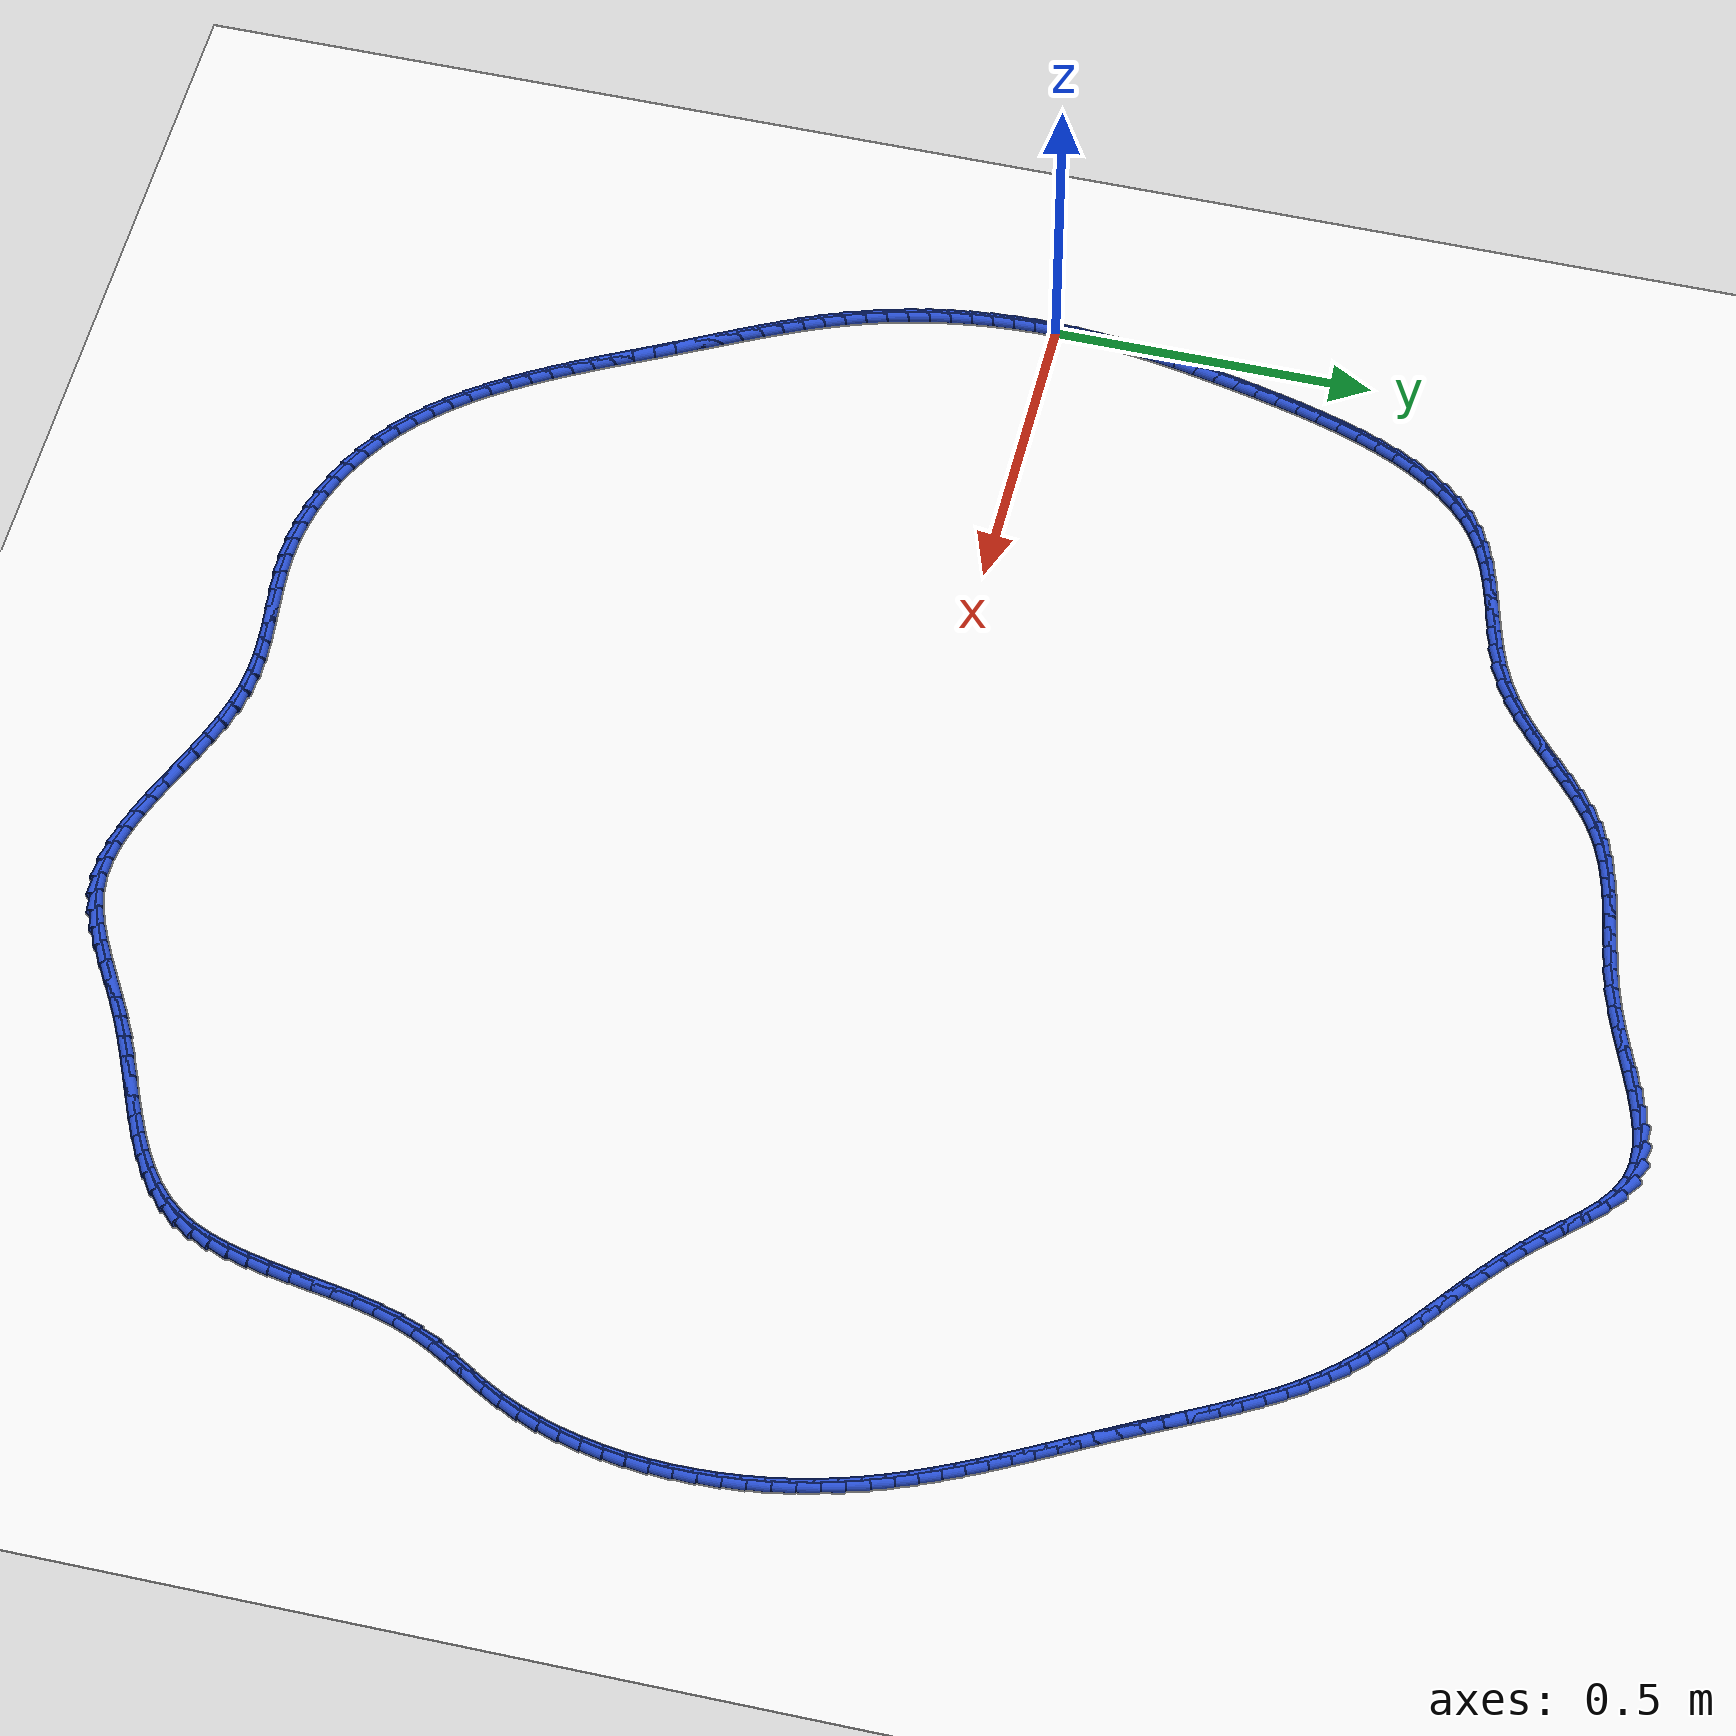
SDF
<sdf version="1.6">
 <world name="default">
  <light name="sun" type="directional">
   <pose>0 0 10 0 -0 0</pose>
   <diffuse>0.8 0.8 0.8 1</diffuse>
   <specular>0.2 0.2 0.2 1</specular>
   <attenuation>
    <range>1000</range>
    <constant>0.9</constant>
    <linear>0.01</linear>
    <quadratic>0.001</quadratic>
   </attenuation>
   <direction>-0.5 0.1 -0.9</direction>
  </light>
  <model name="ground_plane">
   <static>1</static>
   <link name="link">
    <collision name="collision">
     <geometry><plane><normal>0 0 1</normal><size>100 100</size></plane></geometry>
     <surface><friction><ode><mu>100</mu><mu2>50</mu2></ode></friction></surface>
    </collision>
    <visual name="visual">
     <cast_shadows>0</cast_shadows>
     <geometry><plane><normal>0 0 1</normal><size>100 100</size></plane></geometry>
     <material>
      <script><uri>file://media/materials/scripts/gazebo.material</uri><name>Gazebo/WhiteGlow</name></script>
     </material>
    </visual>
   </link>
  </model>
  <gravity>0 0 -9.8</gravity>
  <magnetic_field>6e-06 2.3e-05 -4.2e-05</magnetic_field>
  <atmosphere type="adiabatic"/>
  <physics name="default_physics" default="0" type="ode">
   <max_step_size>0.001</max_step_size>
   <real_time_factor>1</real_time_factor>
   <real_time_update_rate>1000</real_time_update_rate>
  </physics>
  <scene><ambient>0.4 0.4 0.4 1</ambient><background>0.7 0.7 0.7 1</background><shadows>1</shadows></scene>
  <spherical_coordinates>
   <surface_model>EARTH_WGS84</surface_model>
   <latitude_deg>0</latitude_deg>
   <longitude_deg>0</longitude_deg>
   <elevation>0</elevation>
   <heading_deg>0</heading_deg>
  </spherical_coordinates>
  <model name="line">
   <link name="link_0">
    <pose>-1.734723475976807e-18 3.469446951953614e-17 0.01 0 1.57 1.531801911281765</pose>
    <collision name="collision">
     <geometry><cylinder><radius>0.01</radius><length>0.08</length></cylinder></geometry>
    </collision>
    <visual name="visual">
     <material>
      <script><name>Gazebo/Blue</name><uri>file://media/materials/scripts/gazebo.material</uri></script>
     </material>
     <geometry><cylinder><radius>0.01</radius><length>0.08</length></cylinder></geometry>
    </visual>
   </link>
   <link name="link_1">
    <pose>0.0012734789865258829 0.032641429173401716 0.01 0 1.57 1.4968240519907146</pose>
    <collision name="collision">
     <geometry><cylinder><radius>0.01</radius><length>0.08</length></cylinder></geometry>
    </collision>
    <visual name="visual">
     <material>
      <script><name>Gazebo/Blue</name><uri>file://media/materials/scripts/gazebo.material</uri></script>
     </material>
     <geometry><cylinder><radius>0.01</radius><length>0.08</length></cylinder></geometry>
    </visual>
   </link>
   <link name="link_2">
    <pose>0.003676940168216866 0.06507352291375909 0.01 0 1.57 1.464726742741518</pose>
    <collision name="collision">
     <geometry><cylinder><radius>0.01</radius><length>0.08</length></cylinder></geometry>
    </collision>
    <visual name="visual">
     <material>
      <script><name>Gazebo/Blue</name><uri>file://media/materials/scripts/gazebo.material</uri></script>
     </material>
     <geometry><cylinder><radius>0.01</radius><length>0.08</length></cylinder></geometry>
    </visual>
   </link>
   <link name="link_3">
    <pose>0.007118392818827004 0.09739698939090188 0.01 0 1.57 1.4358523234587244</pose>
    <collision name="collision">
     <geometry><cylinder><radius>0.01</radius><length>0.08</length></cylinder></geometry>
    </collision>
    <visual name="visual">
     <material>
      <script><name>Gazebo/Blue</name><uri>file://media/materials/scripts/gazebo.material</uri></script>
     </material>
     <geometry><cylinder><radius>0.01</radius><length>0.08</length></cylinder></geometry>
    </visual>
   </link>
   <link name="link_4">
    <pose>0.011505846212110347 0.1297125367746597 0.01 0 1.57 1.4104528048444238</pose>
    <collision name="collision">
     <geometry><cylinder><radius>0.01</radius><length>0.08</length></cylinder></geometry>
    </collision>
    <visual name="visual">
     <material>
      <script><name>Gazebo/Blue</name><uri>file://media/materials/scripts/gazebo.material</uri></script>
     </material>
     <geometry><cylinder><radius>0.01</radius><length>0.08</length></cylinder></geometry>
    </visual>
   </link>
   <link name="link_5">
    <pose>0.016747309621820958 0.16212087323486224 0.01 0 1.57 1.3886908578574864</pose>
    <collision name="collision">
     <geometry><cylinder><radius>0.01</radius><length>0.08</length></cylinder></geometry>
    </collision>
    <visual name="visual">
     <material>
      <script><name>Gazebo/Blue</name><uri>file://media/materials/scripts/gazebo.material</uri></script>
     </material>
     <geometry><cylinder><radius>0.01</radius><length>0.08</length></cylinder></geometry>
    </visual>
   </link>
   <link name="link_6">
    <pose>0.022750792321712884 0.19472270694133917 0.01 0 1.57 1.3706458397378873</pose>
    <collision name="collision">
     <geometry><cylinder><radius>0.01</radius><length>0.08</length></cylinder></geometry>
    </collision>
    <visual name="visual">
     <material>
      <script><name>Gazebo/Blue</name><uri>file://media/materials/scripts/gazebo.material</uri></script>
     </material>
     <geometry><cylinder><radius>0.01</radius><length>0.08</length></cylinder></geometry>
    </visual>
   </link>
   <link name="link_7">
    <pose>0.029424303585540195 0.22761874606392013 0.01 0 1.57 1.356323066493472</pose>
    <collision name="collision">
     <geometry><cylinder><radius>0.01</radius><length>0.08</length></cylinder></geometry>
    </collision>
    <visual name="visual">
     <material>
      <script><name>Gazebo/Blue</name><uri>file://media/materials/scripts/gazebo.material</uri></script>
     </material>
     <geometry><cylinder><radius>0.01</radius><length>0.08</length></cylinder></geometry>
    </visual>
   </link>
   <link name="link_8">
    <pose>0.03667585268705693 0.26090969877243475 0.01 0 1.57 1.345664667601172</pose>
    <collision name="collision">
     <geometry><cylinder><radius>0.01</radius><length>0.08</length></cylinder></geometry>
    </collision>
    <visual name="visual">
     <material>
      <script><name>Gazebo/Blue</name><uri>file://media/materials/scripts/gazebo.material</uri></script>
     </material>
     <geometry><cylinder><radius>0.01</radius><length>0.08</length></cylinder></geometry>
    </visual>
   </link>
   <link name="link_9">
    <pose>0.044413448900017145 0.29469627323671277 0.01 0 1.57 1.3371464687959038</pose>
    <collision name="collision">
     <geometry><cylinder><radius>0.01</radius><length>0.08</length></cylinder></geometry>
    </collision>
    <visual name="visual">
     <material>
      <script><name>Gazebo/Blue</name><uri>file://media/materials/scripts/gazebo.material</uri></script>
     </material>
     <geometry><cylinder><radius>0.01</radius><length>0.08</length></cylinder></geometry>
    </visual>
   </link>
   <link name="link_10">
    <pose>0.05258213571755998 0.32901897318575263 0.01 0 1.57 1.325019053801191</pose>
    <collision name="collision">
     <geometry><cylinder><radius>0.01</radius><length>0.08</length></cylinder></geometry>
    </collision>
    <visual name="visual">
     <material>
      <script><name>Gazebo/Blue</name><uri>file://media/materials/scripts/gazebo.material</uri></script>
     </material>
     <geometry><cylinder><radius>0.01</radius><length>0.08</length></cylinder></geometry>
    </visual>
   </link>
   <link name="link_11">
    <pose>0.06127586385185051 0.36367623228453894 0.01 0 1.57 1.3078039530621142</pose>
    <collision name="collision">
     <geometry><cylinder><radius>0.01</radius><length>0.08</length></cylinder></geometry>
    </collision>
    <visual name="visual">
     <material>
      <script><name>Gazebo/Blue</name><uri>file://media/materials/scripts/gazebo.material</uri></script>
     </material>
     <geometry><cylinder><radius>0.01</radius><length>0.08</length></cylinder></geometry>
    </visual>
   </link>
   <link name="link_12">
    <pose>0.0706260044056051 0.39840565198054995 0.01 0 1.57 1.2852954788354798</pose>
    <collision name="collision">
     <geometry><cylinder><radius>0.01</radius><length>0.08</length></cylinder></geometry>
    </collision>
    <visual name="visual">
     <material>
      <script><name>Gazebo/Blue</name><uri>file://media/materials/scripts/gazebo.material</uri></script>
     </material>
     <geometry><cylinder><radius>0.01</radius><length>0.08</length></cylinder></geometry>
    </visual>
   </link>
   <link name="link_13">
    <pose>0.08076392848173253 0.432944833720951 0.01 0 1.57 1.2571230382006597</pose>
    <collision name="collision">
     <geometry><cylinder><radius>0.01</radius><length>0.08</length></cylinder></geometry>
    </collision>
    <visual name="visual">
     <material>
      <script><name>Gazebo/Blue</name><uri>file://media/materials/scripts/gazebo.material</uri></script>
     </material>
     <geometry><cylinder><radius>0.01</radius><length>0.08</length></cylinder></geometry>
    </visual>
   </link>
   <link name="link_14">
    <pose>0.0918210071831415 0.46703137895290725 0.01 0 1.57 1.2227530717319732</pose>
    <collision name="collision">
     <geometry><cylinder><radius>0.01</radius><length>0.08</length></cylinder></geometry>
    </collision>
    <visual name="visual">
     <material>
      <script><name>Gazebo/Blue</name><uri>file://media/materials/scripts/gazebo.material</uri></script>
     </material>
     <geometry><cylinder><radius>0.01</radius><length>0.08</length></cylinder></geometry>
    </visual>
   </link>
   <link name="link_15">
    <pose>0.10392861161274072 0.5004028891235841 0.01 0 1.57 1.18148954786675</pose>
    <collision name="collision">
     <geometry><cylinder><radius>0.01</radius><length>0.08</length></cylinder></geometry>
    </collision>
    <visual name="visual">
     <material>
      <script><name>Gazebo/Blue</name><uri>file://media/materials/scripts/gazebo.material</uri></script>
     </material>
     <geometry><cylinder><radius>0.01</radius><length>0.08</length></cylinder></geometry>
    </visual>
   </link>
   <link name="link_16">
    <pose>0.11721811287343892 0.5327969656801468 0.01 0 1.57 1.1324803689764762</pose>
    <collision name="collision">
     <geometry><cylinder><radius>0.01</radius><length>0.08</length></cylinder></geometry>
    </collision>
    <visual name="visual">
     <material>
      <script><name>Gazebo/Blue</name><uri>file://media/materials/scripts/gazebo.material</uri></script>
     </material>
     <geometry><cylinder><radius>0.01</radius><length>0.08</length></cylinder></geometry>
    </visual>
   </link>
   <link name="link_17">
    <pose>0.13182088206814488 0.5639512100697607 0.01 0 1.57 1.074741272115694</pose>
    <collision name="collision">
     <geometry><cylinder><radius>0.01</radius><length>0.08</length></cylinder></geometry>
    </collision>
    <visual name="visual">
     <material>
      <script><name>Gazebo/Blue</name><uri>file://media/materials/scripts/gazebo.material</uri></script>
     </material>
     <geometry><cylinder><radius>0.01</radius><length>0.08</length></cylinder></geometry>
    </visual>
   </link>
   <link name="link_18">
    <pose>0.14786829029976734 0.5936032237395913 0.01 0 1.57 1.0072152260446683</pose>
    <collision name="collision">
     <geometry><cylinder><radius>0.01</radius><length>0.08</length></cylinder></geometry>
    </collision>
    <visual name="visual">
     <material>
      <script><name>Gazebo/Blue</name><uri>file://media/materials/scripts/gazebo.material</uri></script>
     </material>
     <geometry><cylinder><radius>0.01</radius><length>0.08</length></cylinder></geometry>
    </visual>
   </link>
   <link name="link_19">
    <pose>0.16549170867121502 0.6214906081368037 0.01 0 1.57 0.9288925972312421</pose>
    <collision name="collision">
     <geometry><cylinder><radius>0.01</radius><length>0.08</length></cylinder></geometry>
    </collision>
    <visual name="visual">
     <material>
      <script><name>Gazebo/Blue</name><uri>file://media/materials/scripts/gazebo.material</uri></script>
     </material>
     <geometry><cylinder><radius>0.01</radius><length>0.08</length></cylinder></geometry>
    </visual>
   </link>
   <link name="link_20">
    <pose>0.18482250828539662 0.647350964708563 0.01 0 1.57 0.8390202098490814</pose>
    <collision name="collision">
     <geometry><cylinder><radius>0.01</radius><length>0.08</length></cylinder></geometry>
    </collision>
    <visual name="visual">
     <material>
      <script><name>Gazebo/Blue</name><uri>file://media/materials/scripts/gazebo.material</uri></script>
     </material>
     <geometry><cylinder><radius>0.01</radius><length>0.08</length></cylinder></geometry>
    </visual>
   </link>
   <link name="link_21">
    <pose>0.20599206024522093 0.6709218949020351 0.01 0 1.57 0.7374135426826905</pose>
    <collision name="collision">
     <geometry><cylinder><radius>0.01</radius><length>0.08</length></cylinder></geometry>
    </collision>
    <visual name="visual">
     <material>
      <script><name>Gazebo/Blue</name><uri>file://media/materials/scripts/gazebo.material</uri></script>
     </material>
     <geometry><cylinder><radius>0.01</radius><length>0.08</length></cylinder></geometry>
    </visual>
   </link>
   <link name="link_22">
    <pose>0.22913173565359662 0.6919410001643849 0.01 0 1.57 0.6248376676247132</pose>
    <collision name="collision">
     <geometry><cylinder><radius>0.01</radius><length>0.08</length></cylinder></geometry>
    </collision>
    <visual name="visual">
     <material>
      <script><name>Gazebo/Blue</name><uri>file://media/materials/scripts/gazebo.material</uri></script>
     </material>
     <geometry><cylinder><radius>0.01</radius><length>0.08</length></cylinder></geometry>
    </visual>
   </link>
   <link name="link_23">
    <pose>0.2543729056134324 0.7101458819427775 0.01 0 1.57 0.505456203031287</pose>
    <collision name="collision">
     <geometry><cylinder><radius>0.01</radius><length>0.08</length></cylinder></geometry>
    </collision>
    <visual name="visual">
     <material>
      <script><name>Gazebo/Blue</name><uri>file://media/materials/scripts/gazebo.material</uri></script>
     </material>
     <geometry><cylinder><radius>0.01</radius><length>0.08</length></cylinder></geometry>
    </visual>
   </link>
   <link name="link_24">
    <pose>0.281812740319468 0.7253313149945136 0.01 0 1.57 0.4030541246867624</pose>
    <collision name="collision">
     <geometry><cylinder><radius>0.01</radius><length>0.08</length></cylinder></geometry>
    </collision>
    <visual name="visual">
     <material>
      <script><name>Gazebo/Blue</name><uri>file://media/materials/scripts/gazebo.material</uri></script>
     </material>
     <geometry><cylinder><radius>0.01</radius><length>0.08</length></cylinder></geometry>
    </visual>
   </link>
   <link name="link_25">
    <pose>0.3112059698614377 0.7378645277155264 0.01 0 1.57 0.32978577033556566</pose>
    <collision name="collision">
     <geometry><cylinder><radius>0.01</radius><length>0.08</length></cylinder></geometry>
    </collision>
    <visual name="visual">
     <material>
      <script><name>Gazebo/Blue</name><uri>file://media/materials/scripts/gazebo.material</uri></script>
     </material>
     <geometry><cylinder><radius>0.01</radius><length>0.08</length></cylinder></geometry>
    </visual>
   </link>
   <link name="link_26">
    <pose>0.34211004160571235 0.7484425440227146 0.01 0 1.57 0.2837718854165359</pose>
    <collision name="collision">
     <geometry><cylinder><radius>0.01</radius><length>0.08</length></cylinder></geometry>
    </collision>
    <visual name="visual">
     <material>
      <script><name>Gazebo/Blue</name><uri>file://media/materials/scripts/gazebo.material</uri></script>
     </material>
     <geometry><cylinder><radius>0.01</radius><length>0.08</length></cylinder></geometry>
    </visual>
   </link>
   <link name="link_27">
    <pose>0.3740800308030414 0.7577663532745199 0.01 0 1.57 0.262883048818698</pose>
    <collision name="collision">
     <geometry><cylinder><radius>0.01</radius><length>0.08</length></cylinder></geometry>
    </collision>
    <visual name="visual">
     <material>
      <script><name>Gazebo/Blue</name><uri>file://media/materials/scripts/gazebo.material</uri></script>
     </material>
     <geometry><cylinder><radius>0.01</radius><length>0.08</length></cylinder></geometry>
    </visual>
   </link>
   <link name="link_28">
    <pose>0.40667101270417433 0.7665369448293836 0.01 0 1.57 0.26573769492536553</pose>
    <collision name="collision">
     <geometry><cylinder><radius>0.01</radius><length>0.08</length></cylinder></geometry>
    </collision>
    <visual name="visual">
     <material>
      <script><name>Gazebo/Blue</name><uri>file://media/materials/scripts/gazebo.material</uri></script>
     </material>
     <geometry><cylinder><radius>0.01</radius><length>0.08</length></cylinder></geometry>
    </visual>
   </link>
   <link name="link_29">
    <pose>0.4394380625598607 0.7754553080457476 0.01 0 1.57 0.2919554439027531</pose>
    <collision name="collision">
     <geometry><cylinder><radius>0.01</radius><length>0.08</length></cylinder></geometry>
    </collision>
    <visual name="visual">
     <material>
      <script><name>Gazebo/Blue</name><uri>file://media/materials/scripts/gazebo.material</uri></script>
     </material>
     <geometry><cylinder><radius>0.01</radius><length>0.08</length></cylinder></geometry>
    </visual>
   </link>
   <link name="link_30">
    <pose>0.47193625562085056 0.7852224322820535 0.01 0 1.57 0.34205534865502046</pose>
    <collision name="collision">
     <geometry><cylinder><radius>0.01</radius><length>0.08</length></cylinder></geometry>
    </collision>
    <visual name="visual">
     <material>
      <script><name>Gazebo/Blue</name><uri>file://media/materials/scripts/gazebo.material</uri></script>
     </material>
     <geometry><cylinder><radius>0.01</radius><length>0.08</length></cylinder></geometry>
    </visual>
   </link>
   <link name="link_31">
    <pose>0.5037206671378931 0.7965393068967426 0.01 0 1.57 0.41702915107844857</pose>
    <collision name="collision">
     <geometry><cylinder><radius>0.01</radius><length>0.08</length></cylinder></geometry>
    </collision>
    <visual name="visual">
     <material>
      <script><name>Gazebo/Blue</name><uri>file://media/materials/scripts/gazebo.material</uri></script>
     </material>
     <geometry><cylinder><radius>0.01</radius><length>0.08</length></cylinder></geometry>
    </visual>
   </link>
   <link name="link_32">
    <pose>0.5343463723617382 0.8101069212482566 0.01 0 1.57 0.5128569070085608</pose>
    <collision name="collision">
     <geometry><cylinder><radius>0.01</radius><length>0.08</length></cylinder></geometry>
    </collision>
    <visual name="visual">
     <material>
      <script><name>Gazebo/Blue</name><uri>file://media/materials/scripts/gazebo.material</uri></script>
     </material>
     <geometry><cylinder><radius>0.01</radius><length>0.08</length></cylinder></geometry>
    </visual>
   </link>
   <link name="link_33">
    <pose>0.5634428321283611 0.8264915890766877 0.01 0 1.57 0.5981819581872617</pose>
    <collision name="collision">
     <geometry><cylinder><radius>0.01</radius><length>0.08</length></cylinder></geometry>
    </collision>
    <visual name="visual">
     <material>
      <script><name>Gazebo/Blue</name><uri>file://media/materials/scripts/gazebo.material</uri></script>
     </material>
     <geometry><cylinder><radius>0.01</radius><length>0.08</length></cylinder></geometry>
    </visual>
   </link>
   <link name="link_34">
    <pose>0.5911348107306366 0.8453628737755863 0.01 0 1.57 0.6601263199134412</pose>
    <collision name="collision">
     <geometry><cylinder><radius>0.01</radius><length>0.08</length></cylinder></geometry>
    </collision>
    <visual name="visual">
     <material>
      <script><name>Gazebo/Blue</name><uri>file://media/materials/scripts/gazebo.material</uri></script>
     </material>
     <geometry><cylinder><radius>0.01</radius><length>0.08</length></cylinder></geometry>
    </visual>
   </link>
   <link name="link_35">
    <pose>0.6177494187679955 0.8660239893460308 0.01 0 1.57 0.6992605258342632</pose>
    <collision name="collision">
     <geometry><cylinder><radius>0.01</radius><length>0.08</length></cylinder></geometry>
    </collision>
    <visual name="visual">
     <material>
      <script><name>Gazebo/Blue</name><uri>file://media/materials/scripts/gazebo.material</uri></script>
     </material>
     <geometry><cylinder><radius>0.01</radius><length>0.08</length></cylinder></geometry>
    </visual>
   </link>
   <link name="link_36">
    <pose>0.6436143684592758 0.8877770605529852 0.01 0 1.57 0.7162536560897144</pose>
    <collision name="collision">
     <geometry><cylinder><radius>0.01</radius><length>0.08</length></cylinder></geometry>
    </collision>
    <visual name="visual">
     <material>
      <script><name>Gazebo/Blue</name><uri>file://media/materials/scripts/gazebo.material</uri></script>
     </material>
     <geometry><cylinder><radius>0.01</radius><length>0.08</length></cylinder></geometry>
    </visual>
   </link>
   <link name="link_37">
    <pose>0.6690573720233162 0.9099242121614153 0.01 0 1.57 0.7112547116933056</pose>
    <collision name="collision">
     <geometry><cylinder><radius>0.01</radius><length>0.08</length></cylinder></geometry>
    </collision>
    <visual name="visual">
     <material>
      <script><name>Gazebo/Blue</name><uri>file://media/materials/scripts/gazebo.material</uri></script>
     </material>
     <geometry><cylinder><radius>0.01</radius><length>0.08</length></cylinder></geometry>
    </visual>
   </link>
   <link name="link_38">
    <pose>0.6944061416789544 0.9317675689362845 0.01 0 1.57 0.6836362943842442</pose>
    <collision name="collision">
     <geometry><cylinder><radius>0.01</radius><length>0.08</length></cylinder></geometry>
    </collision>
    <visual name="visual">
     <material>
      <script><name>Gazebo/Blue</name><uri>file://media/materials/scripts/gazebo.material</uri></script>
     </material>
     <geometry><cylinder><radius>0.01</radius><length>0.08</length></cylinder></geometry>
    </visual>
   </link>
   <link name="link_39">
    <pose>0.7199883896450288 0.9526092556425585 0.01 0 1.57 0.6320093441488053</pose>
    <collision name="collision">
     <geometry><cylinder><radius>0.01</radius><length>0.08</length></cylinder></geometry>
    </collision>
    <visual name="visual">
     <material>
      <script><name>Gazebo/Blue</name><uri>file://media/materials/scripts/gazebo.material</uri></script>
     </material>
     <geometry><cylinder><radius>0.01</radius><length>0.08</length></cylinder></geometry>
    </visual>
   </link>
   <link name="link_40">
    <pose>0.7461318281403775 0.9717513970452019 0.01 0 1.57 0.5545859695427342</pose>
    <collision name="collision">
     <geometry><cylinder><radius>0.01</radius><length>0.08</length></cylinder></geometry>
    </collision>
    <visual name="visual">
     <material>
      <script><name>Gazebo/Blue</name><uri>file://media/materials/scripts/gazebo.material</uri></script>
     </material>
     <geometry><cylinder><radius>0.01</radius><length>0.08</length></cylinder></geometry>
    </visual>
   </link>
   <link name="link_41">
    <pose>0.7731641693838388 0.9884961179091789 0.01 0 1.57 0.45607324200184807</pose>
    <collision name="collision">
     <geometry><cylinder><radius>0.01</radius><length>0.08</length></cylinder></geometry>
    </collision>
    <visual name="visual">
     <material>
      <script><name>Gazebo/Blue</name><uri>file://media/materials/scripts/gazebo.material</uri></script>
     </material>
     <geometry><cylinder><radius>0.01</radius><length>0.08</length></cylinder></geometry>
    </visual>
   </link>
   <link name="link_42">
    <pose>0.8013508053959618 1.0023235678150995 0.01 0 1.57 0.36544461639054204</pose>
    <collision name="collision">
     <geometry><cylinder><radius>0.01</radius><length>0.08</length></cylinder></geometry>
    </collision>
    <visual name="visual">
     <material>
      <script><name>Gazebo/Blue</name><uri>file://media/materials/scripts/gazebo.material</uri></script>
     </material>
     <geometry><cylinder><radius>0.01</radius><length>0.08</length></cylinder></geometry>
    </visual>
   </link>
   <link name="link_43">
    <pose>0.8306675582209306 1.0135410862928114 0.01 0 1.57 0.29307096880721095</pose>
    <collision name="collision">
     <geometry><cylinder><radius>0.01</radius><length>0.08</length></cylinder></geometry>
    </collision>
    <visual name="visual">
     <material>
      <script><name>Gazebo/Blue</name><uri>file://media/materials/scripts/gazebo.material</uri></script>
     </material>
     <geometry><cylinder><radius>0.01</radius><length>0.08</length></cylinder></geometry>
    </visual>
   </link>
   <link name="link_44">
    <pose>0.8610062085583516 1.022696086640947 0.01 0 1.57 0.23975715989009924</pose>
    <collision name="collision">
     <geometry><cylinder><radius>0.01</radius><length>0.08</length></cylinder></geometry>
    </collision>
    <visual name="visual">
     <material>
      <script><name>Gazebo/Blue</name><uri>file://media/materials/scripts/gazebo.material</uri></script>
     </material>
     <geometry><cylinder><radius>0.01</radius><length>0.08</length></cylinder></geometry>
    </visual>
   </link>
   <link name="link_45">
    <pose>0.8922585280978721 1.0303360078961303 0.01 0 1.57 0.20520348158251472</pose>
    <collision name="collision">
     <geometry><cylinder><radius>0.01</radius><length>0.08</length></cylinder></geometry>
    </collision>
    <visual name="visual">
     <material>
      <script><name>Gazebo/Blue</name><uri>file://media/materials/scripts/gazebo.material</uri></script>
     </material>
     <geometry><cylinder><radius>0.01</radius><length>0.08</length></cylinder></geometry>
    </visual>
   </link>
   <link name="link_46">
    <pose>0.9243162885291387 1.0370082890949839 0.01 0 1.57 0.18860557881183887</pose>
    <collision name="collision">
     <geometry><cylinder><radius>0.01</radius><length>0.08</length></cylinder></geometry>
    </collision>
    <visual name="visual">
     <material>
      <script><name>Gazebo/Blue</name><uri>file://media/materials/scripts/gazebo.material</uri></script>
     </material>
     <geometry><cylinder><radius>0.01</radius><length>0.08</length></cylinder></geometry>
    </visual>
   </link>
   <link name="link_47">
    <pose>0.9570712615417976 1.0432603692741305 0.01 0 1.57 0.18903426544923954</pose>
    <collision name="collision">
     <geometry><cylinder><radius>0.01</radius><length>0.08</length></cylinder></geometry>
    </collision>
    <visual name="visual">
     <material>
      <script><name>Gazebo/Blue</name><uri>file://media/materials/scripts/gazebo.material</uri></script>
     </material>
     <geometry><cylinder><radius>0.01</radius><length>0.08</length></cylinder></geometry>
    </visual>
   </link>
   <link name="link_48">
    <pose>0.9904152188254955 1.0496396874701928 0.01 0 1.57 0.20559882122137657</pose>
    <collision name="collision">
     <geometry><cylinder><radius>0.01</radius><length>0.08</length></cylinder></geometry>
    </collision>
    <visual name="visual">
     <material>
      <script><name>Gazebo/Blue</name><uri>file://media/materials/scripts/gazebo.material</uri></script>
     </material>
     <geometry><cylinder><radius>0.01</radius><length>0.08</length></cylinder></geometry>
    </visual>
   </link>
   <link name="link_49">
    <pose>1.0242399320698794 1.0566936827197941 0.01 0 1.57 0.23744566550088833</pose>
    <collision name="collision">
     <geometry><cylinder><radius>0.01</radius><length>0.08</length></cylinder></geometry>
    </collision>
    <visual name="visual">
     <material>
      <script><name>Gazebo/Blue</name><uri>file://media/materials/scripts/gazebo.material</uri></script>
     </material>
     <geometry><cylinder><radius>0.01</radius><length>0.08</length></cylinder></geometry>
    </visual>
   </link>
   <link name="link_50">
    <pose>1.0584371729645954 1.0649697940595573 0.01 0 1.57 0.2836416951871096</pose>
    <collision name="collision">
     <geometry><cylinder><radius>0.01</radius><length>0.08</length></cylinder></geometry>
    </collision>
    <visual name="visual">
     <material>
      <script><name>Gazebo/Blue</name><uri>file://media/materials/scripts/gazebo.material</uri></script>
     </material>
     <geometry><cylinder><radius>0.01</radius><length>0.08</length></cylinder></geometry>
    </visual>
   </link>
   <link name="link_51">
    <pose>1.0928987082672128 1.0750153762010626 0.01 0 1.57 0.3352020451860106</pose>
    <collision name="collision">
     <geometry><cylinder><radius>0.01</radius><length>0.08</length></cylinder></geometry>
    </collision>
    <visual name="visual">
     <material>
      <script><name>Gazebo/Blue</name><uri>file://media/materials/scripts/gazebo.material</uri></script>
     </material>
     <geometry><cylinder><radius>0.01</radius><length>0.08</length></cylinder></geometry>
    </visual>
   </link>
   <link name="link_52">
    <pose>1.127498187213998 1.087068023781209 0.01 0 1.57 0.367186037776528</pose>
    <collision name="collision">
     <geometry><cylinder><radius>0.01</radius><length>0.08</length></cylinder></geometry>
    </collision>
    <visual name="visual">
     <material>
      <script><name>Gazebo/Blue</name><uri>file://media/materials/scripts/gazebo.material</uri></script>
     </material>
     <geometry><cylinder><radius>0.01</radius><length>0.08</length></cylinder></geometry>
    </visual>
   </link>
   <link name="link_53">
    <pose>1.1620503292554436 1.100357793234586 0.01 0 1.57 0.3762128105053831</pose>
    <collision name="collision">
     <geometry><cylinder><radius>0.01</radius><length>0.08</length></cylinder></geometry>
    </collision>
    <visual name="visual">
     <material>
      <script><name>Gazebo/Blue</name><uri>file://media/materials/scripts/gazebo.material</uri></script>
     </material>
     <geometry><cylinder><radius>0.01</radius><length>0.08</length></cylinder></geometry>
    </visual>
   </link>
   <link name="link_54">
    <pose>1.1963578928346383 1.11391024047476 0.01 0 1.57 0.36241655544991563</pose>
    <collision name="collision">
     <geometry><cylinder><radius>0.01</radius><length>0.08</length></cylinder></geometry>
    </collision>
    <visual name="visual">
     <material>
      <script><name>Gazebo/Blue</name><uri>file://media/materials/scripts/gazebo.material</uri></script>
     </material>
     <geometry><cylinder><radius>0.01</radius><length>0.08</length></cylinder></geometry>
    </visual>
   </link>
   <link name="link_55">
    <pose>1.2302236363946726 1.1267509214152982 0.01 0 1.57 0.3238864352297905</pose>
    <collision name="collision">
     <geometry><cylinder><radius>0.01</radius><length>0.08</length></cylinder></geometry>
    </collision>
    <visual name="visual">
     <material>
      <script><name>Gazebo/Blue</name><uri>file://media/materials/scripts/gazebo.material</uri></script>
     </material>
     <geometry><cylinder><radius>0.01</radius><length>0.08</length></cylinder></geometry>
    </visual>
   </link>
   <link name="link_56">
    <pose>1.2634503183786372 1.1379053919697675 0.01 0 1.57 0.2564582332397891</pose>
    <collision name="collision">
     <geometry><cylinder><radius>0.01</radius><length>0.08</length></cylinder></geometry>
    </collision>
    <visual name="visual">
     <material>
      <script><name>Gazebo/Blue</name><uri>file://media/materials/scripts/gazebo.material</uri></script>
     </material>
     <geometry><cylinder><radius>0.01</radius><length>0.08</length></cylinder></geometry>
    </visual>
   </link>
   <link name="link_57">
    <pose>1.295840697229621 1.1463992080517342 0.01 0 1.57 0.15372672755205324</pose>
    <collision name="collision">
     <geometry><cylinder><radius>0.01</radius><length>0.08</length></cylinder></geometry>
    </collision>
    <visual name="visual">
     <material>
      <script><name>Gazebo/Blue</name><uri>file://media/materials/scripts/gazebo.material</uri></script>
     </material>
     <geometry><cylinder><radius>0.01</radius><length>0.08</length></cylinder></geometry>
    </visual>
   </link>
   <link name="link_58">
    <pose>1.327197531390715 1.151257925574765 0.01 0 1.57 0.008270888917334353</pose>
    <collision name="collision">
     <geometry><cylinder><radius>0.01</radius><length>0.08</length></cylinder></geometry>
    </collision>
    <visual name="visual">
     <material>
      <script><name>Gazebo/Blue</name><uri>file://media/materials/scripts/gazebo.material</uri></script>
     </material>
     <geometry><cylinder><radius>0.01</radius><length>0.08</length></cylinder></geometry>
    </visual>
   </link>
   <link name="link_59">
    <pose>1.357323579305009 1.151507100452427 0.01 0 1.57 -0.18379678768056107</pose>
    <collision name="collision">
     <geometry><cylinder><radius>0.01</radius><length>0.08</length></cylinder></geometry>
    </collision>
    <visual name="visual">
     <material>
      <script><name>Gazebo/Blue</name><uri>file://media/materials/scripts/gazebo.material</uri></script>
     </material>
     <geometry><cylinder><radius>0.01</radius><length>0.08</length></cylinder></geometry>
    </visual>
   </link>
   <link name="link_60">
    <pose>1.386021599415593 1.1461722885982868 0.01 0 1.57 -0.41129019910904013</pose>
    <collision name="collision">
     <geometry><cylinder><radius>0.01</radius><length>0.08</length></cylinder></geometry>
    </collision>
    <visual name="visual">
     <material>
      <script><name>Gazebo/Blue</name><uri>file://media/materials/scripts/gazebo.material</uri></script>
     </material>
     <geometry><cylinder><radius>0.01</radius><length>0.08</length></cylinder></geometry>
    </visual>
   </link>
   <link name="link_61">
    <pose>1.4131144366950752 1.1343553144220757 0.01 0 1.57 -0.6062342366465657</pose>
    <collision name="collision">
     <geometry><cylinder><radius>0.01</radius><length>0.08</length></cylinder></geometry>
    </collision>
    <visual name="visual">
     <material>
      <script><name>Gazebo/Blue</name><uri>file://media/materials/scripts/gazebo.material</uri></script>
     </material>
     <geometry><cylinder><radius>0.01</radius><length>0.08</length></cylinder></geometry>
    </visual>
   </link>
   <link name="link_62">
    <pose>1.4387921316858892 1.1165522428808354 0.01 0 1.57 -0.7278247261144236</pose>
    <collision name="collision">
     <geometry><cylinder><radius>0.01</radius><length>0.08</length></cylinder></geometry>
    </collision>
    <visual name="visual">
     <material>
      <script><name>Gazebo/Blue</name><uri>file://media/materials/scripts/gazebo.material</uri></script>
     </material>
     <geometry><cylinder><radius>0.01</radius><length>0.08</length></cylinder></geometry>
    </visual>
   </link>
   <link name="link_63">
    <pose>1.4635658965819818 1.0944786267903541 0.01 0 1.57 -0.7893918550376261</pose>
    <collision name="collision">
     <geometry><cylinder><radius>0.01</radius><length>0.08</length></cylinder></geometry>
    </collision>
    <visual name="visual">
     <material>
      <script><name>Gazebo/Blue</name><uri>file://media/materials/scripts/gazebo.material</uri></script>
     </material>
     <geometry><cylinder><radius>0.01</radius><length>0.08</length></cylinder></geometry>
    </visual>
   </link>
   <link name="link_64">
    <pose>1.487957773542856 1.0698911403152205 0.01 0 1.57 -0.8016899265698765</pose>
    <collision name="collision">
     <geometry><cylinder><radius>0.01</radius><length>0.08</length></cylinder></geometry>
    </collision>
    <visual name="visual">
     <material>
      <script><name>Gazebo/Blue</name><uri>file://media/materials/scripts/gazebo.material</uri></script>
     </material>
     <geometry><cylinder><radius>0.01</radius><length>0.08</length></cylinder></geometry>
    </visual>
   </link>
   <link name="link_65">
    <pose>1.5124898047280162 1.0445464576200232 0.01 0 1.57 -0.7700968578919272</pose>
    <collision name="collision">
     <geometry><cylinder><radius>0.01</radius><length>0.08</length></cylinder></geometry>
    </collision>
    <visual name="visual">
     <material>
      <script><name>Gazebo/Blue</name><uri>file://media/materials/scripts/gazebo.material</uri></script>
     </material>
     <geometry><cylinder><radius>0.01</radius><length>0.08</length></cylinder></geometry>
    </visual>
   </link>
   <link name="link_66">
    <pose>1.5376601915975374 1.0201347999758636 0.01 0 1.57 -0.7230304148412149</pose>
    <collision name="collision">
     <geometry><cylinder><radius>0.01</radius><length>0.08</length></cylinder></geometry>
    </collision>
    <visual name="visual">
     <material>
      <script><name>Gazebo/Blue</name><uri>file://media/materials/scripts/gazebo.material</uri></script>
     </material>
     <geometry><cylinder><radius>0.01</radius><length>0.08</length></cylinder></geometry>
    </visual>
   </link>
   <link name="link_67">
    <pose>1.5635785636922532 0.9972632942405313 0.01 0 1.57 -0.6847557749656862</pose>
    <collision name="collision">
     <geometry><cylinder><radius>0.01</radius><length>0.08</length></cylinder></geometry>
    </collision>
    <visual name="visual">
     <material>
      <script><name>Gazebo/Blue</name><uri>file://media/materials/scripts/gazebo.material</uri></script>
     </material>
     <geometry><cylinder><radius>0.01</radius><length>0.08</length></cylinder></geometry>
    </visual>
   </link>
   <link name="link_68">
    <pose>1.590038254982863 0.975657433916414 0.01 0 1.57 -0.6565484600885779</pose>
    <collision name="collision">
     <geometry><cylinder><radius>0.01</radius><length>0.08</length></cylinder></geometry>
    </collision>
    <visual name="visual">
     <material>
      <script><name>Gazebo/Blue</name><uri>file://media/materials/scripts/gazebo.material</uri></script>
     </material>
     <geometry><cylinder><radius>0.01</radius><length>0.08</length></cylinder></geometry>
    </visual>
   </link>
   <link name="link_69">
    <pose>1.6168234062047735 0.9550170875410221 0.01 0 1.57 -0.6388182663092193</pose>
    <collision name="collision">
     <geometry><cylinder><radius>0.01</radius><length>0.08</length></cylinder></geometry>
    </collision>
    <visual name="visual">
     <material>
      <script><name>Gazebo/Blue</name><uri>file://media/materials/scripts/gazebo.material</uri></script>
     </material>
     <geometry><cylinder><radius>0.01</radius><length>0.08</length></cylinder></geometry>
    </visual>
   </link>
   <link name="link_70">
    <pose>1.6437181580933908 0.9350421236518687 0.01 0 1.57 -0.6318942539059451</pose>
    <collision name="collision">
     <geometry><cylinder><radius>0.01</radius><length>0.08</length></cylinder></geometry>
    </collision>
    <visual name="visual">
     <material>
      <script><name>Gazebo/Blue</name><uri>file://media/materials/scripts/gazebo.material</uri></script>
     </material>
     <geometry><cylinder><radius>0.01</radius><length>0.08</length></cylinder></geometry>
    </visual>
   </link>
   <link name="link_71">
    <pose>1.6705066513841238 0.9154324107864649 0.01 0 1.57 -0.636080221314197</pose>
    <collision name="collision">
     <geometry><cylinder><radius>0.01</radius><length>0.08</length></cylinder></geometry>
    </collision>
    <visual name="visual">
     <material>
      <script><name>Gazebo/Blue</name><uri>file://media/materials/scripts/gazebo.material</uri></script>
     </material>
     <geometry><cylinder><radius>0.01</radius><length>0.08</length></cylinder></geometry>
    </visual>
   </link>
   <link name="link_72">
    <pose>1.6969730268123795 0.8958878174823226 0.01 0 1.57 -0.6516775976688524</pose>
    <collision name="collision">
     <geometry><cylinder><radius>0.01</radius><length>0.08</length></cylinder></geometry>
    </collision>
    <visual name="visual">
     <material>
      <script><name>Gazebo/Blue</name><uri>file://media/materials/scripts/gazebo.material</uri></script>
     </material>
     <geometry><cylinder><radius>0.01</radius><length>0.08</length></cylinder></geometry>
    </visual>
   </link>
   <link name="link_73">
    <pose>1.7229014251135657 0.8761082122769537 0.01 0 1.57 -0.6789676711831227</pose>
    <collision name="collision">
     <geometry><cylinder><radius>0.01</radius><length>0.08</length></cylinder></geometry>
    </collision>
    <visual name="visual">
     <material>
      <script><name>Gazebo/Blue</name><uri>file://media/materials/scripts/gazebo.material</uri></script>
     </material>
     <geometry><cylinder><radius>0.01</radius><length>0.08</length></cylinder></geometry>
    </visual>
   </link>
   <link name="link_74">
    <pose>1.7480759870230895 0.8557934637078706 0.01 0 1.57 -0.7181455277484654</pose>
    <collision name="collision">
     <geometry><cylinder><radius>0.01</radius><length>0.08</length></cylinder></geometry>
    </collision>
    <visual name="visual">
     <material>
      <script><name>Gazebo/Blue</name><uri>file://media/materials/scripts/gazebo.material</uri></script>
     </material>
     <geometry><cylinder><radius>0.01</radius><length>0.08</length></cylinder></geometry>
    </visual>
   </link>
   <link name="link_75">
    <pose>1.7722808532763583 0.8346434403125842 0.01 0 1.57 -0.7692007974757122</pose>
    <collision name="collision">
     <geometry><cylinder><radius>0.01</radius><length>0.08</length></cylinder></geometry>
    </collision>
    <visual name="visual">
     <material>
      <script><name>Gazebo/Blue</name><uri>file://media/materials/scripts/gazebo.material</uri></script>
     </material>
     <geometry><cylinder><radius>0.01</radius><length>0.08</length></cylinder></geometry>
    </visual>
   </link>
   <link name="link_76">
    <pose>1.795300164608781 0.812358010628607 0.01 0 1.57 -0.8315837573089901</pose>
    <collision name="collision">
     <geometry><cylinder><radius>0.01</radius><length>0.08</length></cylinder></geometry>
    </collision>
    <visual name="visual">
     <material>
      <script><name>Gazebo/Blue</name><uri>file://media/materials/scripts/gazebo.material</uri></script>
     </material>
     <geometry><cylinder><radius>0.01</radius><length>0.08</length></cylinder></geometry>
    </visual>
   </link>
   <link name="link_77">
    <pose>1.8169214849217499 0.7886412331858317 0.01 0 1.57 -0.8963731660071597</pose>
    <collision name="collision">
     <geometry><cylinder><radius>0.01</radius><length>0.08</length></cylinder></geometry>
    </collision>
    <visual name="visual">
     <material>
      <script><name>Gazebo/Blue</name><uri>file://media/materials/scripts/gazebo.material</uri></script>
     </material>
     <geometry><cylinder><radius>0.01</radius><length>0.08</length></cylinder></geometry>
    </visual>
   </link>
   <link name="link_78">
    <pose>1.8370997226552508 0.763401998048567 0.01 0 1.57 -0.9515807476593038</pose>
    <collision name="collision">
     <geometry><cylinder><radius>0.01</radius><length>0.08</length></cylinder></geometry>
    </collision>
    <visual name="visual">
     <material>
      <script><name>Gazebo/Blue</name><uri>file://media/materials/scripts/gazebo.material</uri></script>
     </material>
     <geometry><cylinder><radius>0.01</radius><length>0.08</length></cylinder></geometry>
    </visual>
   </link>
   <link name="link_79">
    <pose>1.8560293805655779 0.7368424613288845 0.01 0 1.57 -0.9965024253885824</pose>
    <collision name="collision">
     <geometry><cylinder><radius>0.01</radius><length>0.08</length></cylinder></geometry>
    </collision>
    <visual name="visual">
     <material>
      <script><name>Gazebo/Blue</name><uri>file://media/materials/scripts/gazebo.material</uri></script>
     </material>
     <geometry><cylinder><radius>0.01</radius><length>0.08</length></cylinder></geometry>
    </visual>
   </link>
   <link name="link_80">
    <pose>1.8739234205205497 0.7091873732920296 0.01 0 1.57 -1.031515620052271</pose>
    <collision name="collision">
     <geometry><cylinder><radius>0.01</radius><length>0.08</length></cylinder></geometry>
    </collision>
    <visual name="visual">
     <material>
      <script><name>Gazebo/Blue</name><uri>file://media/materials/scripts/gazebo.material</uri></script>
     </material>
     <geometry><cylinder><radius>0.01</radius><length>0.08</length></cylinder></geometry>
    </visual>
   </link>
   <link name="link_81">
    <pose>1.890994804387984 0.6806614842032463 0.01 0 1.57 -1.0570414957962166</pose>
    <collision name="collision">
     <geometry><cylinder><radius>0.01</radius><length>0.08</length></cylinder></geometry>
    </collision>
    <visual name="visual">
     <material>
      <script><name>Gazebo/Blue</name><uri>file://media/materials/scripts/gazebo.material</uri></script>
     </material>
     <geometry><cylinder><radius>0.01</radius><length>0.08</length></cylinder></geometry>
    </visual>
   </link>
   <link name="link_82">
    <pose>1.9074564940357004 0.6514895443277791 0.01 0 1.57 -1.073452165395257</pose>
    <collision name="collision">
     <geometry><cylinder><radius>0.01</radius><length>0.08</length></cylinder></geometry>
    </collision>
    <visual name="visual">
     <material>
      <script><name>Gazebo/Blue</name><uri>file://media/materials/scripts/gazebo.material</uri></script>
     </material>
     <geometry><cylinder><radius>0.01</radius><length>0.08</length></cylinder></geometry>
    </visual>
   </link>
   <link name="link_83">
    <pose>1.923521451331517 0.6218963039308727 0.01 0 1.57 -1.0810141594300668</pose>
    <collision name="collision">
     <geometry><cylinder><radius>0.01</radius><length>0.08</length></cylinder></geometry>
    </collision>
    <visual name="visual">
     <material>
      <script><name>Gazebo/Blue</name><uri>file://media/materials/scripts/gazebo.material</uri></script>
     </material>
     <geometry><cylinder><radius>0.01</radius><length>0.08</length></cylinder></geometry>
    </visual>
   </link>
   <link name="link_84">
    <pose>1.9394026381432519 0.5921065132777714 0.01 0 1.57 -1.0798577545190435</pose>
    <collision name="collision">
     <geometry><cylinder><radius>0.01</radius><length>0.08</length></cylinder></geometry>
    </collision>
    <visual name="visual">
     <material>
      <script><name>Gazebo/Blue</name><uri>file://media/materials/scripts/gazebo.material</uri></script>
     </material>
     <geometry><cylinder><radius>0.01</radius><length>0.08</length></cylinder></geometry>
    </visual>
   </link>
   <link name="link_85">
    <pose>1.9553130163387242 0.5623449226337194 0.01 0 1.57 -1.070672349839233</pose>
    <collision name="collision">
     <geometry><cylinder><radius>0.01</radius><length>0.08</length></cylinder></geometry>
    </collision>
    <visual name="visual">
     <material>
      <script><name>Gazebo/Blue</name><uri>file://media/materials/scripts/gazebo.material</uri></script>
     </material>
     <geometry><cylinder><radius>0.01</radius><length>0.08</length></cylinder></geometry>
    </visual>
   </link>
   <link name="link_86">
    <pose>1.9714473516591176 0.5328199205711985 0.01 0 1.57 -1.061091811210459</pose>
    <collision name="collision">
     <geometry><cylinder><radius>0.01</radius><length>0.08</length></cylinder></geometry>
    </collision>
    <visual name="visual">
     <material>
      <script><name>Gazebo/Blue</name><uri>file://media/materials/scripts/gazebo.material</uri></script>
     </material>
     <geometry><cylinder><radius>0.01</radius><length>0.08</length></cylinder></geometry>
    </visual>
   </link>
   <link name="link_87">
    <pose>1.987801974819627 0.5035614657696744 0.01 0 1.57 -1.0558931195700973</pose>
    <collision name="collision">
     <geometry><cylinder><radius>0.01</radius><length>0.08</length></cylinder></geometry>
    </collision>
    <visual name="visual">
     <material>
      <script><name>Gazebo/Blue</name><uri>file://media/materials/scripts/gazebo.material</uri></script>
     </material>
     <geometry><cylinder><radius>0.01</radius><length>0.08</length></cylinder></geometry>
    </visual>
   </link>
   <link name="link_88">
    <pose>2.0042511495227027 0.47448975602382654 0.01 0 1.57 -1.0551968677047787</pose>
    <collision name="collision">
     <geometry><cylinder><radius>0.01</radius><length>0.08</length></cylinder></geometry>
    </collision>
    <visual name="visual">
     <material>
      <script><name>Gazebo/Blue</name><uri>file://media/materials/scripts/gazebo.material</uri></script>
     </material>
     <geometry><cylinder><radius>0.01</radius><length>0.08</length></cylinder></geometry>
    </visual>
   </link>
   <link name="link_89">
    <pose>2.020667356599426 0.4455233859962996 0.01 0 1.57 -1.0590475110282096</pose>
    <collision name="collision">
     <geometry><cylinder><radius>0.01</radius><length>0.08</length></cylinder></geometry>
    </collision>
    <visual name="visual">
     <material>
      <script><name>Gazebo/Blue</name><uri>file://media/materials/scripts/gazebo.material</uri></script>
     </material>
     <geometry><cylinder><radius>0.01</radius><length>0.08</length></cylinder></geometry>
    </visual>
   </link>
   <link name="link_90">
    <pose>2.0369230768808797 0.41658095034973774 0.01 0 1.57 -1.067482902166082</pose>
    <collision name="collision">
     <geometry><cylinder><radius>0.01</radius><length>0.08</length></cylinder></geometry>
    </collision>
    <visual name="visual">
     <material>
      <script><name>Gazebo/Blue</name><uri>file://media/materials/scripts/gazebo.material</uri></script>
     </material>
     <geometry><cylinder><radius>0.01</radius><length>0.08</length></cylinder></geometry>
    </visual>
   </link>
   <link name="link_91">
    <pose>2.0528907911981484 0.3875810437467857 0.01 0 1.57 -1.0805316544826453</pose>
    <collision name="collision">
     <geometry><cylinder><radius>0.01</radius><length>0.08</length></cylinder></geometry>
    </collision>
    <visual name="visual">
     <material>
      <script><name>Gazebo/Blue</name><uri>file://media/materials/scripts/gazebo.material</uri></script>
     </material>
     <geometry><cylinder><radius>0.01</radius><length>0.08</length></cylinder></geometry>
    </visual>
   </link>
   <link name="link_92">
    <pose>2.068442980382315 0.3584422608500875 0.01 0 1.57 -1.0982075534994828</pose>
    <collision name="collision">
     <geometry><cylinder><radius>0.01</radius><length>0.08</length></cylinder></geometry>
    </collision>
    <visual name="visual">
     <material>
      <script><name>Gazebo/Blue</name><uri>file://media/materials/scripts/gazebo.material</uri></script>
     </material>
     <geometry><cylinder><radius>0.01</radius><length>0.08</length></cylinder></geometry>
    </visual>
   </link>
   <link name="link_93">
    <pose>2.08345212526446 0.3290831963222882 0.01 0 1.57 -1.120500999814698</pose>
    <collision name="collision">
     <geometry><cylinder><radius>0.01</radius><length>0.08</length></cylinder></geometry>
    </collision>
    <visual name="visual">
     <material>
      <script><name>Gazebo/Blue</name><uri>file://media/materials/scripts/gazebo.material</uri></script>
     </material>
     <geometry><cylinder><radius>0.01</radius><length>0.08</length></cylinder></geometry>
    </visual>
   </link>
   <link name="link_94">
    <pose>2.0977907066756694 0.299422444826032 0.01 0 1.57 -1.1473676706369809</pose>
    <collision name="collision">
     <geometry><cylinder><radius>0.01</radius><length>0.08</length></cylinder></geometry>
    </collision>
    <visual name="visual">
     <material>
      <script><name>Gazebo/Blue</name><uri>file://media/materials/scripts/gazebo.material</uri></script>
     </material>
     <geometry><cylinder><radius>0.01</radius><length>0.08</length></cylinder></geometry>
    </visual>
   </link>
   <link name="link_95">
    <pose>2.1113312054470246 0.26937860102396294 0.01 0 1.57 -1.1787149221556432</pose>
    <collision name="collision">
     <geometry><cylinder><radius>0.01</radius><length>0.08</length></cylinder></geometry>
    </collision>
    <visual name="visual">
     <material>
      <script><name>Gazebo/Blue</name><uri>file://media/materials/scripts/gazebo.material</uri></script>
     </material>
     <geometry><cylinder><radius>0.01</radius><length>0.08</length></cylinder></geometry>
    </visual>
   </link>
   <link name="link_96">
    <pose>2.123946102409608 0.2388702595787262 0.01 0 1.57 -1.2143869374222098</pose>
    <collision name="collision">
     <geometry><cylinder><radius>0.01</radius><length>0.08</length></cylinder></geometry>
    </collision>
    <visual name="visual">
     <material>
      <script><name>Gazebo/Blue</name><uri>file://media/materials/scripts/gazebo.material</uri></script>
     </material>
     <geometry><cylinder><radius>0.01</radius><length>0.08</length></cylinder></geometry>
    </visual>
   </link>
   <link name="link_97">
    <pose>2.1355078783945043 0.20781601515296597 0.01 0 1.57 -1.2541502210737032</pose>
    <collision name="collision">
     <geometry><cylinder><radius>0.01</radius><length>0.08</length></cylinder></geometry>
    </collision>
    <visual name="visual">
     <material>
      <script><name>Gazebo/Blue</name><uri>file://media/materials/scripts/gazebo.material</uri></script>
     </material>
     <geometry><cylinder><radius>0.01</radius><length>0.08</length></cylinder></geometry>
    </visual>
   </link>
   <link name="link_98">
    <pose>2.1458890142327958 0.1761344624093263 0.01 0 1.57 -1.2973289870470863</pose>
    <collision name="collision">
     <geometry><cylinder><radius>0.01</radius><length>0.08</length></cylinder></geometry>
    </collision>
    <visual name="visual">
     <material>
      <script><name>Gazebo/Blue</name><uri>file://media/materials/scripts/gazebo.material</uri></script>
     </material>
     <geometry><cylinder><radius>0.01</radius><length>0.08</length></cylinder></geometry>
    </visual>
   </link>
   <link name="link_99">
    <pose>2.1549694914208324 0.14376137810756445 0.01 0 1.57 -1.3411361033142222</pose>
    <collision name="collision">
     <geometry><cylinder><radius>0.01</radius><length>0.08</length></cylinder></geometry>
    </collision>
    <visual name="visual">
     <material>
      <script><name>Gazebo/Blue</name><uri>file://media/materials/scripts/gazebo.material</uri></script>
     </material>
     <geometry><cylinder><radius>0.01</radius><length>0.08</length></cylinder></geometry>
    </visual>
   </link>
   <link name="link_100">
    <pose>2.1626847931680593 0.11075967917304792 0.01 0 1.57 -1.3846608863334027</pose>
    <collision name="collision">
     <geometry><cylinder><radius>0.01</radius><length>0.08</length></cylinder></geometry>
    </collision>
    <visual name="visual">
     <material>
      <script><name>Gazebo/Blue</name><uri>file://media/materials/scripts/gazebo.material</uri></script>
     </material>
     <geometry><cylinder><radius>0.01</radius><length>0.08</length></cylinder></geometry>
    </visual>
   </link>
   <link name="link_101">
    <pose>2.168995305000204 0.07724932734002724 0.01 0 1.57 -1.4282187004355398</pose>
    <collision name="collision">
     <geometry><cylinder><radius>0.01</radius><length>0.08</length></cylinder></geometry>
    </collision>
    <visual name="visual">
     <material>
      <script><name>Gazebo/Blue</name><uri>file://media/materials/scripts/gazebo.material</uri></script>
     </material>
     <geometry><cylinder><radius>0.01</radius><length>0.08</length></cylinder></geometry>
    </visual>
   </link>
   <link name="link_102">
    <pose>2.17386153047113 0.043350554714889224 0.01 0 1.57 -1.4721203783231147</pose>
    <collision name="collision">
     <geometry><cylinder><radius>0.01</radius><length>0.08</length></cylinder></geometry>
    </collision>
    <visual name="visual">
     <material>
      <script><name>Gazebo/Blue</name><uri>file://media/materials/scripts/gazebo.material</uri></script>
     </material>
     <geometry><cylinder><radius>0.01</radius><length>0.08</length></cylinder></geometry>
    </visual>
   </link>
   <link name="link_103">
    <pose>2.1772439731346993 0.009183593404019204 0.01 0 1.57 -1.5166697957087492</pose>
    <collision name="collision">
     <geometry><cylinder><radius>0.01</radius><length>0.08</length></cylinder></geometry>
    </collision>
    <visual name="visual">
     <material>
      <script><name>Gazebo/Blue</name><uri>file://media/materials/scripts/gazebo.material</uri></script>
     </material>
     <geometry><cylinder><radius>0.01</radius><length>0.08</length></cylinder></geometry>
    </visual>
   </link>
   <link name="link_104">
    <pose>2.1791031365447746 -0.02513132448619691 0.01 0 1.57 -1.5621662292883387</pose>
    <collision name="collision">
     <geometry><cylinder><radius>0.01</radius><length>0.08</length></cylinder></geometry>
    </collision>
    <visual name="visual">
     <material>
      <script><name>Gazebo/Blue</name><uri>file://media/materials/scripts/gazebo.material</uri></script>
     </material>
     <geometry><cylinder><radius>0.01</radius><length>0.08</length></cylinder></geometry>
    </visual>
   </link>
   <link name="link_105">
    <pose>2.179399524255217 -0.05947396684937325 0.01 0 1.57 1.5326869238924696</pose>
    <collision name="collision">
     <geometry><cylinder><radius>0.01</radius><length>0.08</length></cylinder></geometry>
    </collision>
    <visual name="visual">
     <material>
      <script><name>Gazebo/Blue</name><uri>file://media/materials/scripts/gazebo.material</uri></script>
     </material>
     <geometry><cylinder><radius>0.01</radius><length>0.08</length></cylinder></geometry>
    </visual>
   </link>
   <link name="link_106">
    <pose>2.178093639819891 -0.0937241015791248 0.01 0 1.57 1.484411418783419</pose>
    <collision name="collision">
     <geometry><cylinder><radius>0.01</radius><length>0.08</length></cylinder></geometry>
    </collision>
    <visual name="visual">
     <material>
      <script><name>Gazebo/Blue</name><uri>file://media/materials/scripts/gazebo.material</uri></script>
     </material>
     <geometry><cylinder><radius>0.01</radius><length>0.08</length></cylinder></geometry>
    </visual>
   </link>
   <link name="link_107">
    <pose>2.175145986792658 -0.1277614965690641 0.01 0 1.57 1.4343115794018848</pose>
    <collision name="collision">
     <geometry><cylinder><radius>0.01</radius><length>0.08</length></cylinder></geometry>
    </collision>
    <visual name="visual">
     <material>
      <script><name>Gazebo/Blue</name><uri>file://media/materials/scripts/gazebo.material</uri></script>
     </material>
     <geometry><cylinder><radius>0.01</radius><length>0.08</length></cylinder></geometry>
    </visual>
   </link>
   <link name="link_108">
    <pose>2.170517068727382 -0.1614659197128061 0.01 0 1.57 1.3821072164647787</pose>
    <collision name="collision">
     <geometry><cylinder><radius>0.01</radius><length>0.08</length></cylinder></geometry>
    </collision>
    <visual name="visual">
     <material>
      <script><name>Gazebo/Blue</name><uri>file://media/materials/scripts/gazebo.material</uri></script>
     </material>
     <geometry><cylinder><radius>0.01</radius><length>0.08</length></cylinder></geometry>
    </visual>
   </link>
   <link name="link_109">
    <pose>2.164167389177924 -0.194717138903965 0.01 0 1.57 1.3275323383912978</pose>
    <collision name="collision">
     <geometry><cylinder><radius>0.01</radius><length>0.08</length></cylinder></geometry>
    </collision>
    <visual name="visual">
     <material>
      <script><name>Gazebo/Blue</name><uri>file://media/materials/scripts/gazebo.material</uri></script>
     </material>
     <geometry><cylinder><radius>0.01</radius><length>0.08</length></cylinder></geometry>
    </visual>
   </link>
   <link name="link_110">
    <pose>2.156057451698147 -0.2273949220361548 0.01 0 1.57 1.2703442328906775</pose>
    <collision name="collision">
     <geometry><cylinder><radius>0.01</radius><length>0.08</length></cylinder></geometry>
    </collision>
    <visual name="visual">
     <material>
      <script><name>Gazebo/Blue</name><uri>file://media/materials/scripts/gazebo.material</uri></script>
     </material>
     <geometry><cylinder><radius>0.01</radius><length>0.08</length></cylinder></geometry>
    </visual>
   </link>
   <link name="link_111">
    <pose>2.146147759841914 -0.2593790370029898 0.01 0 1.57 1.210335978209612</pose>
    <collision name="collision">
     <geometry><cylinder><radius>0.01</radius><length>0.08</length></cylinder></geometry>
    </collision>
    <visual name="visual">
     <material>
      <script><name>Gazebo/Blue</name><uri>file://media/materials/scripts/gazebo.material</uri></script>
     </material>
     <geometry><cylinder><radius>0.01</radius><length>0.08</length></cylinder></geometry>
    </visual>
   </link>
   <link name="link_112">
    <pose>2.1343988171630865 -0.29054925169808477 0.01 0 1.57 1.1473525254350045</pose>
    <collision name="collision">
     <geometry><cylinder><radius>0.01</radius><length>0.08</length></cylinder></geometry>
    </collision>
    <visual name="visual">
     <material>
      <script><name>Gazebo/Blue</name><uri>file://media/materials/scripts/gazebo.material</uri></script>
     </material>
     <geometry><cylinder><radius>0.01</radius><length>0.08</length></cylinder></geometry>
    </visual>
   </link>
   <link name="link_113">
    <pose>2.1207711272155287 -0.3207853340150525 0.01 0 1.57 1.082526620550699</pose>
    <collision name="collision">
     <geometry><cylinder><radius>0.01</radius><length>0.08</length></cylinder></geometry>
    </collision>
    <visual name="visual">
     <material>
      <script><name>Gazebo/Blue</name><uri>file://media/materials/scripts/gazebo.material</uri></script>
     </material>
     <geometry><cylinder><radius>0.01</radius><length>0.08</length></cylinder></geometry>
    </visual>
   </link>
   <link name="link_114">
    <pose>2.1052586085443754 -0.3499898975086852 0.01 0 1.57 1.0357120804103066</pose>
    <collision name="collision">
     <geometry><cylinder><radius>0.01</radius><length>0.08</length></cylinder></geometry>
    </collision>
    <visual name="visual">
     <material>
      <script><name>Gazebo/Blue</name><uri>file://media/materials/scripts/gazebo.material</uri></script>
     </material>
     <geometry><cylinder><radius>0.01</radius><length>0.08</length></cylinder></geometry>
    </visual>
   </link>
   <link name="link_115">
    <pose>2.0883967839410094 -0.378435847828143 0.01 0 1.57 1.0231244885910853</pose>
    <collision name="collision">
     <geometry><cylinder><radius>0.01</radius><length>0.08</length></cylinder></geometry>
    </collision>
    <visual name="visual">
     <material>
      <script><name>Gazebo/Blue</name><uri>file://media/materials/scripts/gazebo.material</uri></script>
     </material>
     <geometry><cylinder><radius>0.01</radius><length>0.08</length></cylinder></geometry>
    </visual>
   </link>
   <link name="link_116">
    <pose>2.071160470083566 -0.4066964336396454 0.01 0 1.57 1.0451556700630134</pose>
    <collision name="collision">
     <geometry><cylinder><radius>0.01</radius><length>0.08</length></cylinder></geometry>
    </collision>
    <visual name="visual">
     <material>
      <script><name>Gazebo/Blue</name><uri>file://media/materials/scripts/gazebo.material</uri></script>
     </material>
     <geometry><cylinder><radius>0.01</radius><length>0.08</length></cylinder></geometry>
    </visual>
   </link>
   <link name="link_117">
    <pose>2.0545371549868676 -0.4353535669384605 0.01 0 1.57 1.1016293000730044</pose>
    <collision name="collision">
     <geometry><cylinder><radius>0.01</radius><length>0.08</length></cylinder></geometry>
    </collision>
    <visual name="visual">
     <material>
      <script><name>Gazebo/Blue</name><uri>file://media/materials/scripts/gazebo.material</uri></script>
     </material>
     <geometry><cylinder><radius>0.01</radius><length>0.08</length></cylinder></geometry>
    </visual>
   </link>
   <link name="link_118">
    <pose>2.0395143266657354 -0.46498915971985694 0.01 0 1.57 1.1870695892729743</pose>
    <collision name="collision">
     <geometry><cylinder><radius>0.01</radius><length>0.08</length></cylinder></geometry>
    </collision>
    <visual name="visual">
     <material>
      <script><name>Gazebo/Blue</name><uri>file://media/materials/scripts/gazebo.material</uri></script>
     </material>
     <geometry><cylinder><radius>0.01</radius><length>0.08</length></cylinder></geometry>
    </visual>
   </link>
   <link name="link_119">
    <pose>2.0269517643707675 -0.49610460113404165 0.01 0 1.57 1.266709615179039</pose>
    <collision name="collision">
     <geometry><cylinder><radius>0.01</radius><length>0.08</length></cylinder></geometry>
    </collision>
    <visual name="visual">
     <material>
      <script><name>Gazebo/Blue</name><uri>file://media/materials/scripts/gazebo.material</uri></script>
     </material>
     <geometry><cylinder><radius>0.01</radius><length>0.08</length></cylinder></geometry>
    </visual>
   </link>
   <link name="link_120">
    <pose>2.0167543242550163 -0.5285991828549951 0.01 0 1.57 1.3262465700602</pose>
    <collision name="collision">
     <geometry><cylinder><radius>0.01</radius><length>0.08</length></cylinder></geometry>
    </collision>
    <visual name="visual">
     <material>
      <script><name>Gazebo/Blue</name><uri>file://media/materials/scripts/gazebo.material</uri></script>
     </material>
     <geometry><cylinder><radius>0.01</radius><length>0.08</length></cylinder></geometry>
    </visual>
   </link>
   <link name="link_121">
    <pose>2.0083944904848825 -0.5620995776593029 0.01 0 1.57 1.3670542230160794</pose>
    <collision name="collision">
     <geometry><cylinder><radius>0.01</radius><length>0.08</length></cylinder></geometry>
    </collision>
    <visual name="visual">
     <material>
      <script><name>Gazebo/Blue</name><uri>file://media/materials/scripts/gazebo.material</uri></script>
     </material>
     <geometry><cylinder><radius>0.01</radius><length>0.08</length></cylinder></geometry>
    </visual>
   </link>
   <link name="link_122">
    <pose>2.001342612257167 -0.5962311121839374 0.01 0 1.57 1.3903458527604275</pose>
    <collision name="collision">
     <geometry><cylinder><radius>0.01</radius><length>0.08</length></cylinder></geometry>
    </collision>
    <visual name="visual">
     <material>
      <script><name>Gazebo/Blue</name><uri>file://media/materials/scripts/gazebo.material</uri></script>
     </material>
     <geometry><cylinder><radius>0.01</radius><length>0.08</length></cylinder></geometry>
    </visual>
   </link>
   <link name="link_123">
    <pose>1.9950690387686671 -0.6306191130658704 0.01 0 1.57 1.396766335321182</pose>
    <collision name="collision">
     <geometry><cylinder><radius>0.01</radius><length>0.08</length></cylinder></geometry>
    </collision>
    <visual name="visual">
     <material>
      <script><name>Gazebo/Blue</name><uri>file://media/materials/scripts/gazebo.material</uri></script>
     </material>
     <geometry><cylinder><radius>0.01</radius><length>0.08</length></cylinder></geometry>
    </visual>
   </link>
   <link name="link_124">
    <pose>1.9890441192161843 -0.6648889069420741 0.01 0 1.57 1.3862279942010143</pose>
    <collision name="collision">
     <geometry><cylinder><radius>0.01</radius><length>0.08</length></cylinder></geometry>
    </collision>
    <visual name="visual">
     <material>
      <script><name>Gazebo/Blue</name><uri>file://media/materials/scripts/gazebo.material</uri></script>
     </material>
     <geometry><cylinder><radius>0.01</radius><length>0.08</length></cylinder></geometry>
    </visual>
   </link>
   <link name="link_125">
    <pose>1.9827382027965175 -0.6986658204495219 0.01 0 1.57 1.3578281688381069</pose>
    <collision name="collision">
     <geometry><cylinder><radius>0.01</radius><length>0.08</length></cylinder></geometry>
    </collision>
    <visual name="visual">
     <material>
      <script><name>Gazebo/Blue</name><uri>file://media/materials/scripts/gazebo.material</uri></script>
     </material>
     <geometry><cylinder><radius>0.01</radius><length>0.08</length></cylinder></geometry>
    </visual>
   </link>
   <link name="link_126">
    <pose>1.9756216387064656 -0.7315751802251836 0.01 0 1.57 1.3098315230164528</pose>
    <collision name="collision">
     <geometry><cylinder><radius>0.01</radius><length>0.08</length></cylinder></geometry>
    </collision>
    <visual name="visual">
     <material>
      <script><name>Gazebo/Blue</name><uri>file://media/materials/scripts/gazebo.material</uri></script>
     </material>
     <geometry><cylinder><radius>0.01</radius><length>0.08</length></cylinder></geometry>
    </visual>
   </link>
   <link name="link_127">
    <pose>1.96716477614283 -0.7632423129060327 0.01 0 1.57 1.2397882107973113</pose>
    <collision name="collision">
     <geometry><cylinder><radius>0.01</radius><length>0.08</length></cylinder></geometry>
    </collision>
    <visual name="visual">
     <material>
      <script><name>Gazebo/Blue</name><uri>file://media/materials/scripts/gazebo.material</uri></script>
     </material>
     <geometry><cylinder><radius>0.01</radius><length>0.08</length></cylinder></geometry>
    </visual>
   </link>
   <link name="link_128">
    <pose>1.9568379643024092 -0.7932925451290413 0.01 0 1.57 1.1449821006005845</pose>
    <collision name="collision">
     <geometry><cylinder><radius>0.01</radius><length>0.08</length></cylinder></geometry>
    </collision>
    <visual name="visual">
     <material>
      <script><name>Gazebo/Blue</name><uri>file://media/materials/scripts/gazebo.material</uri></script>
     </material>
     <geometry><cylinder><radius>0.01</radius><length>0.08</length></cylinder></geometry>
    </visual>
   </link>
   <link name="link_129">
    <pose>1.944111552382003 -0.8213512035311812 0.01 0 1.57 1.0235304026594017</pose>
    <collision name="collision">
     <geometry><cylinder><radius>0.01</radius><length>0.08</length></cylinder></geometry>
    </collision>
    <visual name="visual">
     <material>
      <script><name>Gazebo/Blue</name><uri>file://media/materials/scripts/gazebo.material</uri></script>
     </material>
     <geometry><cylinder><radius>0.01</radius><length>0.08</length></cylinder></geometry>
    </visual>
   </link>
   <link name="link_130">
    <pose>1.9284558895784119 -0.8470436147494251 0.01 0 1.57 0.8811891530363578</pose>
    <collision name="collision">
     <geometry><cylinder><radius>0.01</radius><length>0.08</length></cylinder></geometry>
    </collision>
    <visual name="visual">
     <material>
      <script><name>Gazebo/Blue</name><uri>file://media/materials/scripts/gazebo.material</uri></script>
     </material>
     <geometry><cylinder><radius>0.01</radius><length>0.08</length></cylinder></geometry>
    </visual>
   </link>
   <link name="link_131">
    <pose>1.9094539627592708 -0.8700853049938193 0.01 0 1.57 0.749073279238194</pose>
    <collision name="collision">
     <geometry><cylinder><radius>0.01</radius><length>0.08</length></cylinder></geometry>
    </collision>
    <visual name="visual">
     <material>
      <script><name>Gazebo/Blue</name><uri>file://media/materials/scripts/gazebo.material</uri></script>
     </material>
     <geometry><cylinder><radius>0.01</radius><length>0.08</length></cylinder></geometry>
    </visual>
   </link>
   <link name="link_132">
    <pose>1.8873024638849003 -0.8906832518418162 0.01 0 1.57 0.6397748678084795</pose>
    <collision name="collision">
     <geometry><cylinder><radius>0.01</radius><length>0.08</length></cylinder></geometry>
    </collision>
    <visual name="visual">
     <material>
      <script><name>Gazebo/Blue</name><uri>file://media/materials/scripts/gazebo.material</uri></script>
     </material>
     <geometry><cylinder><radius>0.01</radius><length>0.08</length></cylinder></geometry>
    </visual>
   </link>
   <link name="link_133">
    <pose>1.8624060773831774 -0.9092109919947979 0.01 0 1.57 0.553525718419027</pose>
    <collision name="collision">
     <geometry><cylinder><radius>0.01</radius><length>0.08</length></cylinder></geometry>
    </collision>
    <visual name="visual">
     <material>
      <script><name>Gazebo/Blue</name><uri>file://media/materials/scripts/gazebo.material</uri></script>
     </material>
     <geometry><cylinder><radius>0.01</radius><length>0.08</length></cylinder></geometry>
    </visual>
   </link>
   <link name="link_134">
    <pose>1.8351696548976661 -0.9260421960594719 0.01 0 1.57 0.48862591407132816</pose>
    <collision name="collision">
     <geometry><cylinder><radius>0.01</radius><length>0.08</length></cylinder></geometry>
    </collision>
    <visual name="visual">
     <material>
      <script><name>Gazebo/Blue</name><uri>file://media/materials/scripts/gazebo.material</uri></script>
     </material>
     <geometry><cylinder><radius>0.01</radius><length>0.08</length></cylinder></geometry>
    </visual>
   </link>
   <link name="link_135">
    <pose>1.8059980480719295 -0.9415505346425437 0.01 0 1.57 0.4428029575286789</pose>
    <collision name="collision">
     <geometry><cylinder><radius>0.01</radius><length>0.08</length></cylinder></geometry>
    </collision>
    <visual name="visual">
     <material>
      <script><name>Gazebo/Blue</name><uri>file://media/materials/scripts/gazebo.material</uri></script>
     </material>
     <geometry><cylinder><radius>0.01</radius><length>0.08</length></cylinder></geometry>
    </visual>
   </link>
   <link name="link_136">
    <pose>1.775296108549532 -0.9561096783507195 0.01 0 1.57 0.4139685518748146</pose>
    <collision name="collision">
     <geometry><cylinder><radius>0.01</radius><length>0.08</length></cylinder></geometry>
    </collision>
    <visual name="visual">
     <material>
      <script><name>Gazebo/Blue</name><uri>file://media/materials/scripts/gazebo.material</uri></script>
     </material>
     <geometry><cylinder><radius>0.01</radius><length>0.08</length></cylinder></geometry>
    </visual>
   </link>
   <link name="link_137">
    <pose>1.7434686879740369 -0.9700932977907054 0.01 0 1.57 0.4005386585146003</pose>
    <collision name="collision">
     <geometry><cylinder><radius>0.01</radius><length>0.08</length></cylinder></geometry>
    </collision>
    <visual name="visual">
     <material>
      <script><name>Gazebo/Blue</name><uri>file://media/materials/scripts/gazebo.material</uri></script>
     </material>
     <geometry><cylinder><radius>0.01</radius><length>0.08</length></cylinder></geometry>
    </visual>
   </link>
   <link name="link_138">
    <pose>1.710920637989008 -0.983875063569208 0.01 0 1.57 0.4015215203887412</pose>
    <collision name="collision">
     <geometry><cylinder><radius>0.01</radius><length>0.08</length></cylinder></geometry>
    </collision>
    <visual name="visual">
     <material>
      <script><name>Gazebo/Blue</name><uri>file://media/materials/scripts/gazebo.material</uri></script>
     </material>
     <geometry><cylinder><radius>0.01</radius><length>0.08</length></cylinder></geometry>
    </visual>
   </link>
   <link name="link_139">
    <pose>1.6780568102380098 -0.9978286462929323 0.01 0 1.57 0.4165035487182162</pose>
    <collision name="collision">
     <geometry><cylinder><radius>0.01</radius><length>0.08</length></cylinder></geometry>
    </collision>
    <visual name="visual">
     <material>
      <script><name>Gazebo/Blue</name><uri>file://media/materials/scripts/gazebo.material</uri></script>
     </material>
     <geometry><cylinder><radius>0.01</radius><length>0.08</length></cylinder></geometry>
    </visual>
   </link>
   <link name="link_140">
    <pose>1.6452820563646056 -1.012327716568585 0.01 0 1.57 0.4455903875848305</pose>
    <collision name="collision">
     <geometry><cylinder><radius>0.01</radius><length>0.08</length></cylinder></geometry>
    </collision>
    <visual name="visual">
     <material>
      <script><name>Gazebo/Blue</name><uri>file://media/materials/scripts/gazebo.material</uri></script>
     </material>
     <geometry><cylinder><radius>0.01</radius><length>0.08</length></cylinder></geometry>
    </visual>
   </link>
   <link name="link_141">
    <pose>1.6130012280123593 -1.0277459450028719 0.01 0 1.57 0.4839576707132134</pose>
    <collision name="collision">
     <geometry><cylinder><radius>0.01</radius><length>0.08</length></cylinder></geometry>
    </collision>
    <visual name="visual">
     <material>
      <script><name>Gazebo/Blue</name><uri>file://media/materials/scripts/gazebo.material</uri></script>
     </material>
     <geometry><cylinder><radius>0.01</radius><length>0.08</length></cylinder></geometry>
    </visual>
   </link>
   <link name="link_142">
    <pose>1.5815327051236479 -1.0442874243170732 0.01 0 1.57 0.5078225578851494</pose>
    <collision name="collision">
     <geometry><cylinder><radius>0.01</radius><length>0.08</length></cylinder></geometry>
    </collision>
    <visual name="visual">
     <material>
      <script><name>Gazebo/Blue</name><uri>file://media/materials/scripts/gazebo.material</uri></script>
     </material>
     <geometry><cylinder><radius>0.01</radius><length>0.08</length></cylinder></geometry>
    </visual>
   </link>
   <link name="link_143">
    <pose>1.5508033368497531 -1.0613884242022564 0.01 0 1.57 0.5100358530088271</pose>
    <collision name="collision">
     <geometry><cylinder><radius>0.01</radius><length>0.08</length></cylinder></geometry>
    </collision>
    <visual name="visual">
     <material>
      <script><name>Gazebo/Blue</name><uri>file://media/materials/scripts/gazebo.material</uri></script>
     </material>
     <geometry><cylinder><radius>0.01</radius><length>0.08</length></cylinder></geometry>
    </visual>
   </link>
   <link name="link_144">
    <pose>1.5206292119066438 -1.0782680043241095 0.01 0 1.57 0.48949691939724654</pose>
    <collision name="collision">
     <geometry><cylinder><radius>0.01</radius><length>0.08</length></cylinder></geometry>
    </collision>
    <visual name="visual">
     <material>
      <script><name>Gazebo/Blue</name><uri>file://media/materials/scripts/gazebo.material</uri></script>
     </material>
     <geometry><cylinder><radius>0.01</radius><length>0.08</length></cylinder></geometry>
    </visual>
   </link>
   <link name="link_145">
    <pose>1.4908264121092816 -1.0941452108148992 0.01 0 1.57 0.44418001916704</pose>
    <collision name="collision">
     <geometry><cylinder><radius>0.01</radius><length>0.08</length></cylinder></geometry>
    </collision>
    <visual name="visual">
     <material>
      <script><name>Gazebo/Blue</name><uri>file://media/materials/scripts/gazebo.material</uri></script>
     </material>
     <geometry><cylinder><radius>0.01</radius><length>0.08</length></cylinder></geometry>
    </visual>
   </link>
   <link name="link_146">
    <pose>1.4612110192726298 -1.108239089806891 0.01 0 1.57 0.3712977090462093</pose>
    <collision name="collision">
     <geometry><cylinder><radius>0.01</radius><length>0.08</length></cylinder></geometry>
    </collision>
    <visual name="visual">
     <material>
      <script><name>Gazebo/Blue</name><uri>file://media/materials/scripts/gazebo.material</uri></script>
     </material>
     <geometry><cylinder><radius>0.01</radius><length>0.08</length></cylinder></geometry>
    </visual>
   </link>
   <link name="link_147">
    <pose>1.4315991152116498 -1.1197686874323503 0.01 0 1.57 0.26810002783524844</pose>
    <collision name="collision">
     <geometry><cylinder><radius>0.01</radius><length>0.08</length></cylinder></geometry>
    </collision>
    <visual name="visual">
     <material>
      <script><name>Gazebo/Blue</name><uri>file://media/materials/scripts/gazebo.material</uri></script>
     </material>
     <geometry><cylinder><radius>0.01</radius><length>0.08</length></cylinder></geometry>
    </visual>
   </link>
   <link name="link_148">
    <pose>1.4018067817413036 -1.1279530498235428 0.01 0 1.57 0.134702487430526</pose>
    <collision name="collision">
     <geometry><cylinder><radius>0.01</radius><length>0.08</length></cylinder></geometry>
    </collision>
    <visual name="visual">
     <material>
      <script><name>Gazebo/Blue</name><uri>file://media/materials/scripts/gazebo.material</uri></script>
     </material>
     <geometry><cylinder><radius>0.01</radius><length>0.08</length></cylinder></geometry>
    </visual>
   </link>
   <link name="link_149">
    <pose>1.37165458684654 -1.1320393705287457 0.01 0 1.57 -0.0033845972890788802</pose>
    <collision name="collision">
     <geometry><cylinder><radius>0.01</radius><length>0.08</length></cylinder></geometry>
    </collision>
    <visual name="visual">
     <material>
      <script><name>Gazebo/Blue</name><uri>file://media/materials/scripts/gazebo.material</uri></script>
     </material>
     <geometry><cylinder><radius>0.01</radius><length>0.08</length></cylinder></geometry>
    </visual>
   </link>
   <link name="link_150">
    <pose>1.341068450352019 -1.1319358483787834 0.01 0 1.57 -0.11936520780689518</pose>
    <collision name="collision">
     <geometry><cylinder><radius>0.01</radius><length>0.08</length></cylinder></geometry>
    </collision>
    <visual name="visual">
     <material>
      <script><name>Gazebo/Blue</name><uri>file://media/materials/scripts/gazebo.material</uri></script>
     </material>
     <geometry><cylinder><radius>0.01</radius><length>0.08</length></cylinder></geometry>
    </visual>
   </link>
   <link name="link_151">
    <pose>1.310080863728498 -1.1282193408746655 0.01 0 1.57 -0.21123699735171084</pose>
    <collision name="collision">
     <geometry><cylinder><radius>0.01</radius><length>0.08</length></cylinder></geometry>
    </collision>
    <visual name="visual">
     <material>
      <script><name>Gazebo/Blue</name><uri>file://media/materials/scripts/gazebo.material</uri></script>
     </material>
     <geometry><cylinder><radius>0.01</radius><length>0.08</length></cylinder></geometry>
    </visual>
   </link>
   <link name="link_152">
    <pose>1.2787290485881393 -1.1214963836745304 0.01 0 1.57 -0.2803932385159081</pose>
    <collision name="collision">
     <geometry><cylinder><radius>0.01</radius><length>0.08</length></cylinder></geometry>
    </collision>
    <visual name="visual">
     <material>
      <script><name>Gazebo/Blue</name><uri>file://media/materials/scripts/gazebo.material</uri></script>
     </material>
     <geometry><cylinder><radius>0.01</radius><length>0.08</length></cylinder></geometry>
    </visual>
   </link>
   <link name="link_153">
    <pose>1.2470502265431005 -1.112373512436516 0.01 0 1.57 -0.3290536110986142</pose>
    <collision name="collision">
     <geometry><cylinder><radius>0.01</radius><length>0.08</length></cylinder></geometry>
    </collision>
    <visual name="visual">
     <material>
      <script><name>Gazebo/Blue</name><uri>file://media/materials/scripts/gazebo.material</uri></script>
     </material>
     <geometry><cylinder><radius>0.01</radius><length>0.08</length></cylinder></geometry>
    </visual>
   </link>
   <link name="link_154">
    <pose>1.215081619205542 -1.1014572628187598 0.01 0 1.57 -0.35931891016359624</pose>
    <collision name="collision">
     <geometry><cylinder><radius>0.01</radius><length>0.08</length></cylinder></geometry>
    </collision>
    <visual name="visual">
     <material>
      <script><name>Gazebo/Blue</name><uri>file://media/materials/scripts/gazebo.material</uri></script>
     </material>
     <geometry><cylinder><radius>0.01</radius><length>0.08</length></cylinder></geometry>
    </visual>
   </link>
   <link name="link_155">
    <pose>1.182860448187623 -1.0893541704794005 0.01 0 1.57 -0.3727430881619935</pose>
    <collision name="collision">
     <geometry><cylinder><radius>0.01</radius><length>0.08</length></cylinder></geometry>
    </collision>
    <visual name="visual">
     <material>
      <script><name>Gazebo/Blue</name><uri>file://media/materials/scripts/gazebo.material</uri></script>
     </material>
     <geometry><cylinder><radius>0.01</radius><length>0.08</length></cylinder></geometry>
    </visual>
   </link>
   <link name="link_156">
    <pose>1.1504239351015029 -1.0766707710765755 0.01 0 1.57 -0.3701907032382105</pose>
    <collision name="collision">
     <geometry><cylinder><radius>0.01</radius><length>0.08</length></cylinder></geometry>
    </collision>
    <visual name="visual">
     <material>
      <script><name>Gazebo/Blue</name><uri>file://media/materials/scripts/gazebo.material</uri></script>
     </material>
     <geometry><cylinder><radius>0.01</radius><length>0.08</length></cylinder></geometry>
    </visual>
   </link>
   <link name="link_157">
    <pose>1.1178093015593398 -1.064013600268422 0.01 0 1.57 -0.3518226999836894</pose>
    <collision name="collision">
     <geometry><cylinder><radius>0.01</radius><length>0.08</length></cylinder></geometry>
    </collision>
    <visual name="visual">
     <material>
      <script><name>Gazebo/Blue</name><uri>file://media/materials/scripts/gazebo.material</uri></script>
     </material>
     <geometry><cylinder><radius>0.01</radius><length>0.08</length></cylinder></geometry>
    </visual>
   </link>
   <link name="link_158">
    <pose>1.0850537691732955 -1.0519891937130794 0.01 0 1.57 -0.317143078946963</pose>
    <collision name="collision">
     <geometry><cylinder><radius>0.01</radius><length>0.08</length></cylinder></geometry>
    </collision>
    <visual name="visual">
     <material>
      <script><name>Gazebo/Blue</name><uri>file://media/materials/scripts/gazebo.material</uri></script>
     </material>
     <geometry><cylinder><radius>0.01</radius><length>0.08</length></cylinder></geometry>
    </visual>
   </link>
   <link name="link_159">
    <pose>1.0521945595555289 -1.041204087068685 0.01 0 1.57 -0.2651080554753769</pose>
    <collision name="collision">
     <geometry><cylinder><radius>0.01</radius><length>0.08</length></cylinder></geometry>
    </collision>
    <visual name="visual">
     <material>
      <script><name>Gazebo/Blue</name><uri>file://media/materials/scripts/gazebo.material</uri></script>
     </material>
     <geometry><cylinder><radius>0.01</radius><length>0.08</length></cylinder></geometry>
    </visual>
   </link>
   <link name="link_160">
    <pose>1.0192688943181987 -1.0322648159933765 0.01 0 1.57 -0.19435693926992034</pose>
    <collision name="collision">
     <geometry><cylinder><radius>0.01</radius><length>0.08</length></cylinder></geometry>
    </collision>
    <visual name="visual">
     <material>
      <script><name>Gazebo/Blue</name><uri>file://media/materials/scripts/gazebo.material</uri></script>
     </material>
     <geometry><cylinder><radius>0.01</radius><length>0.08</length></cylinder></geometry>
    </visual>
   </link>
   <link name="link_161">
    <pose>0.986313995073465 -1.0257779161452922 0.01 0 1.57 -0.10504484219172666</pose>
    <collision name="collision">
     <geometry><cylinder><radius>0.01</radius><length>0.08</length></cylinder></geometry>
    </collision>
    <visual name="visual">
     <material>
      <script><name>Gazebo/Blue</name><uri>file://media/materials/scripts/gazebo.material</uri></script>
     </material>
     <geometry><cylinder><radius>0.01</radius><length>0.08</length></cylinder></geometry>
    </visual>
   </link>
   <link name="link_162">
    <pose>0.9533651121642364 -1.0223040190517916 0.01 0 1.57 -0.018707043438933306</pose>
    <collision name="collision">
     <geometry><cylinder><radius>0.01</radius><length>0.08</length></cylinder></geometry>
    </collision>
    <visual name="visual">
     <material>
      <script><name>Gazebo/Blue</name><uri>file://media/materials/scripts/gazebo.material</uri></script>
     </material>
     <geometry><cylinder><radius>0.01</radius><length>0.08</length></cylinder></geometry>
    </visual>
   </link>
   <link name="link_163">
    <pose>0.9204267491134619 -1.0216877677752911 0.01 0 1.57 0.04608839262753677</pose>
    <collision name="collision">
     <geometry><cylinder><radius>0.01</radius><length>0.08</length></cylinder></geometry>
    </collision>
    <visual name="visual">
     <material>
      <script><name>Gazebo/Blue</name><uri>file://media/materials/scripts/gazebo.material</uri></script>
     </material>
     <geometry><cylinder><radius>0.01</radius><length>0.08</length></cylinder></geometry>
    </visual>
   </link>
   <link name="link_164">
    <pose>0.8874790839980099 -1.0232073487879236 0.01 0 1.57 0.08825837757708857</pose>
    <collision name="collision">
     <geometry><cylinder><radius>0.01</radius><length>0.08</length></cylinder></geometry>
    </collision>
    <visual name="visual">
     <material>
      <script><name>Gazebo/Blue</name><uri>file://media/materials/scripts/gazebo.material</uri></script>
     </material>
     <geometry><cylinder><radius>0.01</radius><length>0.08</length></cylinder></geometry>
    </visual>
   </link>
   <link name="link_165">
    <pose>0.854501630034697 -1.0261254662410464 0.01 0 1.57 0.107953009109686</pose>
    <collision name="collision">
     <geometry><cylinder><radius>0.01</radius><length>0.08</length></cylinder></geometry>
    </collision>
    <visual name="visual">
     <material>
      <script><name>Gazebo/Blue</name><uri>file://media/materials/scripts/gazebo.material</uri></script>
     </material>
     <geometry><cylinder><radius>0.01</radius><length>0.08</length></cylinder></geometry>
    </visual>
   </link>
   <link name="link_166">
    <pose>0.821473900440338 -1.029704824286019 0.01 0 1.57 0.1054521574742702</pose>
    <collision name="collision">
     <geometry><cylinder><radius>0.01</radius><length>0.08</length></cylinder></geometry>
    </collision>
    <visual name="visual">
     <material>
      <script><name>Gazebo/Blue</name><uri>file://media/materials/scripts/gazebo.material</uri></script>
     </material>
     <geometry><cylinder><radius>0.01</radius><length>0.08</length></cylinder></geometry>
    </visual>
   </link>
   <link name="link_167">
    <pose>0.7883754084317486 -1.0332081270741995 0.01 0 1.57 0.0808709208696169</pose>
    <collision name="collision">
     <geometry><cylinder><radius>0.01</radius><length>0.08</length></cylinder></geometry>
    </collision>
    <visual name="visual">
     <material>
      <script><name>Gazebo/Blue</name><uri>file://media/materials/scripts/gazebo.material</uri></script>
     </material>
     <geometry><cylinder><radius>0.01</radius><length>0.08</length></cylinder></geometry>
    </visual>
   </link>
   <link name="link_168">
    <pose>0.7551856672257441 -1.035898078756947 0.01 0 1.57 0.0341984991990946</pose>
    <collision name="collision">
     <geometry><cylinder><radius>0.01</radius><length>0.08</length></cylinder></geometry>
    </collision>
    <visual name="visual">
     <material>
      <script><name>Gazebo/Blue</name><uri>file://media/materials/scripts/gazebo.material</uri></script>
     </material>
     <geometry><cylinder><radius>0.01</radius><length>0.08</length></cylinder></geometry>
    </visual>
   </link>
   <link name="link_169">
    <pose>0.72188419003914 -1.0370373834856192 0.01 0 1.57 -0.03327782857558497</pose>
    <collision name="collision">
     <geometry><cylinder><radius>0.01</radius><length>0.08</length></cylinder></geometry>
    </collision>
    <visual name="visual">
     <material>
      <script><name>Gazebo/Blue</name><uri>file://media/materials/scripts/gazebo.material</uri></script>
     </material>
     <geometry><cylinder><radius>0.01</radius><length>0.08</length></cylinder></geometry>
    </visual>
   </link>
   <link name="link_170">
    <pose>0.6884614063734097 -1.0359247350691818 0.01 0 1.57 -0.10748569274588807</pose>
    <collision name="collision">
     <geometry><cylinder><radius>0.01</radius><length>0.08</length></cylinder></geometry>
    </collision>
    <visual name="visual">
     <material>
      <script><name>Gazebo/Blue</name><uri>file://media/materials/scripts/gazebo.material</uri></script>
     </material>
     <geometry><cylinder><radius>0.01</radius><length>0.08</length></cylinder></geometry>
    </visual>
   </link>
   <link name="link_171">
    <pose>0.6550474193337882 -1.032319314133588 0.01 0 1.57 -0.1795082823335587</pose>
    <collision name="collision">
     <geometry><cylinder><radius>0.01</radius><length>0.08</length></cylinder></geometry>
    </collision>
    <visual name="visual">
     <material>
      <script><name>Gazebo/Blue</name><uri>file://media/materials/scripts/gazebo.material</uri></script>
     </material>
     <geometry><cylinder><radius>0.01</radius><length>0.08</length></cylinder></geometry>
    </visual>
   </link>
   <link name="link_172">
    <pose>0.6218689043806639 -1.0262986885679417 0.01 0 1.57 -0.24995819140910272</pose>
    <collision name="collision">
     <geometry><cylinder><radius>0.01</radius><length>0.08</length></cylinder></geometry>
    </collision>
    <visual name="visual">
     <material>
      <script><name>Gazebo/Blue</name><uri>file://media/materials/scripts/gazebo.material</uri></script>
     </material>
     <geometry><cylinder><radius>0.01</radius><length>0.08</length></cylinder></geometry>
    </visual>
   </link>
   <link name="link_173">
    <pose>0.5891544633376703 -1.017946777245746 0.01 0 1.57 -0.3196511660445638</pose>
    <collision name="collision">
     <geometry><cylinder><radius>0.01</radius><length>0.08</length></cylinder></geometry>
    </collision>
    <visual name="visual">
     <material>
      <script><name>Gazebo/Blue</name><uri>file://media/materials/scripts/gazebo.material</uri></script>
     </material>
     <geometry><cylinder><radius>0.01</radius><length>0.08</length></cylinder></geometry>
    </visual>
   </link>
   <link name="link_174">
    <pose>0.5571326980284405 -1.007347499040503 0.01 0 1.57 -0.38941446802875695</pose>
    <collision name="collision">
     <geometry><cylinder><radius>0.01</radius><length>0.08</length></cylinder></geometry>
    </collision>
    <visual name="visual">
     <material>
      <script><name>Gazebo/Blue</name><uri>file://media/materials/scripts/gazebo.material</uri></script>
     </material>
     <geometry><cylinder><radius>0.01</radius><length>0.08</length></cylinder></geometry>
    </visual>
   </link>
   <link name="link_175">
    <pose>0.5260322102766071 -0.994584772825715 0.01 0 1.57 -0.46008747809611117</pose>
    <collision name="collision">
     <geometry><cylinder><radius>0.01</radius><length>0.08</length></cylinder></geometry>
    </collision>
    <visual name="visual">
     <material>
      <script><name>Gazebo/Blue</name><uri>file://media/materials/scripts/gazebo.material</uri></script>
     </material>
     <geometry><cylinder><radius>0.01</radius><length>0.08</length></cylinder></geometry>
    </visual>
   </link>
   <link name="link_176">
    <pose>0.4960816019058028 -0.9797425174748842 0.01 0 1.57 -0.5325227827558483</pose>
    <collision name="collision">
     <geometry><cylinder><radius>0.01</radius><length>0.08</length></cylinder></geometry>
    </collision>
    <visual name="visual">
     <material>
      <script><name>Gazebo/Blue</name><uri>file://media/materials/scripts/gazebo.material</uri></script>
     </material>
     <geometry><cylinder><radius>0.01</radius><length>0.08</length></cylinder></geometry>
    </visual>
   </link>
   <link name="link_177">
    <pose>0.46750947473966215 -0.9629046518615137 0.01 0 1.57 -0.6071250379056446</pose>
    <collision name="collision">
     <geometry><cylinder><radius>0.01</radius><length>0.08</length></cylinder></geometry>
    </collision>
    <visual name="visual">
     <material>
      <script><name>Gazebo/Blue</name><uri>file://media/materials/scripts/gazebo.material</uri></script>
     </material>
     <geometry><cylinder><radius>0.01</radius><length>0.08</length></cylinder></geometry>
    </visual>
   </link>
   <link name="link_178">
    <pose>0.44052368982653917 -0.9441590280035221 0.01 0 1.57 -0.6796679332932389</pose>
    <collision name="collision">
     <geometry><cylinder><radius>0.01</radius><length>0.08</length></cylinder></geometry>
    </collision>
    <visual name="visual">
     <material>
      <script><name>Gazebo/Blue</name><uri>file://media/materials/scripts/gazebo.material</uri></script>
     </material>
     <geometry><cylinder><radius>0.01</radius><length>0.08</length></cylinder></geometry>
    </visual>
   </link>
   <link name="link_179">
    <pose>0.4151237355220129 -0.923633012347882 0.01 0 1.57 -0.7468246686328377</pose>
    <collision name="collision">
     <geometry><cylinder><radius>0.01</radius><length>0.08</length></cylinder></geometry>
    </collision>
    <visual name="visual">
     <material>
      <script><name>Gazebo/Blue</name><uri>file://media/materials/scripts/gazebo.material</uri></script>
     </material>
     <geometry><cylinder><radius>0.01</radius><length>0.08</length></cylinder></geometry>
    </visual>
   </link>
   <link name="link_180">
    <pose>0.39118873774221646 -0.901476796084148 0.01 0 1.57 -0.8079686852646707</pose>
    <collision name="collision">
     <geometry><cylinder><radius>0.01</radius><length>0.08</length></cylinder></geometry>
    </collision>
    <visual name="visual">
     <material>
      <script><name>Gazebo/Blue</name><uri>file://media/materials/scripts/gazebo.material</uri></script>
     </material>
     <geometry><cylinder><radius>0.01</radius><length>0.08</length></cylinder></geometry>
    </visual>
   </link>
   <link name="link_181">
    <pose>0.3685963633450769 -0.8778408470880926 0.01 0 1.57 -0.8627862288350491</pose>
    <collision name="collision">
     <geometry><cylinder><radius>0.01</radius><length>0.08</length></cylinder></geometry>
    </collision>
    <visual name="visual">
     <material>
      <script><name>Gazebo/Blue</name><uri>file://media/materials/scripts/gazebo.material</uri></script>
     </material>
     <geometry><cylinder><radius>0.01</radius><length>0.08</length></cylinder></geometry>
    </visual>
   </link>
   <link name="link_182">
    <pose>0.347224279188521 -0.8528756332354879 0.01 0 1.57 -0.9111871729204295</pose>
    <collision name="collision">
     <geometry><cylinder><radius>0.01</radius><length>0.08</length></cylinder></geometry>
    </collision>
    <visual name="visual">
     <material>
      <script><name>Gazebo/Blue</name><uri>file://media/materials/scripts/gazebo.material</uri></script>
     </material>
     <geometry><cylinder><radius>0.01</radius><length>0.08</length></cylinder></geometry>
    </visual>
   </link>
   <link name="link_183">
    <pose>0.3269501521304753 -0.8267316224021048 0.01 0 1.57 -0.9532401756201432</pose>
    <collision name="collision">
     <geometry><cylinder><radius>0.01</radius><length>0.08</length></cylinder></geometry>
    </collision>
    <visual name="visual">
     <material>
      <script><name>Gazebo/Blue</name><uri>file://media/materials/scripts/gazebo.material</uri></script>
     </material>
     <geometry><cylinder><radius>0.01</radius><length>0.08</length></cylinder></geometry>
    </visual>
   </link>
   <link name="link_184">
    <pose>0.30765164902886755 -0.7995592824637169 0.01 0 1.57 -0.9891118726335821</pose>
    <collision name="collision">
     <geometry><cylinder><radius>0.01</radius><length>0.08</length></cylinder></geometry>
    </collision>
    <visual name="visual">
     <material>
      <script><name>Gazebo/Blue</name><uri>file://media/materials/scripts/gazebo.material</uri></script>
     </material>
     <geometry><cylinder><radius>0.01</radius><length>0.08</length></cylinder></geometry>
    </visual>
   </link>
   <link name="link_185">
    <pose>0.2892064367416242 -0.7715090812960955 0.01 0 1.57 -1.0190161969683507</pose>
    <collision name="collision">
     <geometry><cylinder><radius>0.01</radius><length>0.08</length></cylinder></geometry>
    </collision>
    <visual name="visual">
     <material>
      <script><name>Gazebo/Blue</name><uri>file://media/materials/scripts/gazebo.material</uri></script>
     </material>
     <geometry><cylinder><radius>0.01</radius><length>0.08</length></cylinder></geometry>
    </visual>
   </link>
   <link name="link_186">
    <pose>0.27149218212667225 -0.7427314867750123 0.01 0 1.57 -1.043175441588428</pose>
    <collision name="collision">
     <geometry><cylinder><radius>0.01</radius><length>0.08</length></cylinder></geometry>
    </collision>
    <visual name="visual">
     <material>
      <script><name>Gazebo/Blue</name><uri>file://media/materials/scripts/gazebo.material</uri></script>
     </material>
     <geometry><cylinder><radius>0.01</radius><length>0.08</length></cylinder></geometry>
    </visual>
   </link>
   <link name="link_187">
    <pose>0.2543865520419385 -0.7133769667762395 0.01 0 1.57 -1.061792066565423</pose>
    <collision name="collision">
     <geometry><cylinder><radius>0.01</radius><length>0.08</length></cylinder></geometry>
    </collision>
    <visual name="visual">
     <material>
      <script><name>Gazebo/Blue</name><uri>file://media/materials/scripts/gazebo.material</uri></script>
     </material>
     <geometry><cylinder><radius>0.01</radius><length>0.08</length></cylinder></geometry>
    </visual>
   </link>
   <link name="link_188">
    <pose>0.23776721334535 -0.6835959891755491 0.01 0 1.57 -1.0750291462058392</pose>
    <collision name="collision">
     <geometry><cylinder><radius>0.01</radius><length>0.08</length></cylinder></geometry>
    </collision>
    <visual name="visual">
     <material>
      <script><name>Gazebo/Blue</name><uri>file://media/materials/scripts/gazebo.material</uri></script>
     </material>
     <geometry><cylinder><radius>0.01</radius><length>0.08</length></cylinder></geometry>
    </visual>
   </link>
   <link name="link_189">
    <pose>0.2215118328948331 -0.6535390218487122 0.01 0 1.57 -1.082997194441731</pose>
    <collision name="collision">
     <geometry><cylinder><radius>0.01</radius><length>0.08</length></cylinder></geometry>
    </collision>
    <visual name="visual">
     <material>
      <script><name>Gazebo/Blue</name><uri>file://media/materials/scripts/gazebo.material</uri></script>
     </material>
     <geometry><cylinder><radius>0.01</radius><length>0.08</length></cylinder></geometry>
    </visual>
   </link>
   <link name="link_190">
    <pose>0.20549807754831553 -0.6233565326715022 0.01 0 1.57 -1.085745435608422</pose>
    <collision name="collision">
     <geometry><cylinder><radius>0.01</radius><length>0.08</length></cylinder></geometry>
    </collision>
    <visual name="visual">
     <material>
      <script><name>Gazebo/Blue</name><uri>file://media/materials/scripts/gazebo.material</uri></script>
     </material>
     <geometry><cylinder><radius>0.01</radius><length>0.08</length></cylinder></geometry>
    </visual>
   </link>
   <link name="link_191">
    <pose>0.1896036141637238 -0.5931989895196904 0.01 0 1.57 -1.0832561160133454</pose>
    <collision name="collision">
     <geometry><cylinder><radius>0.01</radius><length>0.08</length></cylinder></geometry>
    </collision>
    <visual name="visual">
     <material>
      <script><name>Gazebo/Blue</name><uri>file://media/materials/scripts/gazebo.material</uri></script>
     </material>
     <geometry><cylinder><radius>0.01</radius><length>0.08</length></cylinder></geometry>
    </visual>
   </link>
   <link name="link_192">
    <pose>0.17370610960091662 -0.5632168602672704 0.01 0 1.57 -1.0772854036147592</pose>
    <collision name="collision">
     <geometry><cylinder><radius>0.01</radius><length>0.08</length></cylinder></geometry>
    </collision>
    <visual name="visual">
     <material>
      <script><name>Gazebo/Blue</name><uri>file://media/materials/scripts/gazebo.material</uri></script>
     </material>
     <geometry><cylinder><radius>0.01</radius><length>0.08</length></cylinder></geometry>
    </visual>
   </link>
   <link name="link_193">
    <pose>0.15773044238636422 -0.533517145422705 0.01 0 1.57 -1.075096764328752</pose>
    <collision name="collision">
     <geometry><cylinder><radius>0.01</radius><length>0.08</length></cylinder></geometry>
    </collision>
    <visual name="visual">
     <material>
      <script><name>Gazebo/Blue</name><uri>file://media/materials/scripts/gazebo.material</uri></script>
     </material>
     <geometry><cylinder><radius>0.01</radius><length>0.08</length></cylinder></geometry>
    </visual>
   </link>
   <link name="link_194">
    <pose>0.14178838887878084 -0.5040347703068165 0.01 0 1.57 -1.078588999723382</pose>
    <collision name="collision">
     <geometry><cylinder><radius>0.01</radius><length>0.08</length></cylinder></geometry>
    </collision>
    <visual name="visual">
     <material>
      <script><name>Gazebo/Blue</name><uri>file://media/materials/scripts/gazebo.material</uri></script>
     </material>
     <geometry><cylinder><radius>0.01</radius><length>0.08</length></cylinder></geometry>
    </visual>
   </link>
   <link name="link_195">
    <pose>0.1260379677037892 -0.4746620853926631 0.01 0 1.57 -1.0878517275900605</pose>
    <collision name="collision">
     <geometry><cylinder><radius>0.01</radius><length>0.08</length></cylinder></geometry>
    </collision>
    <visual name="visual">
     <material>
      <script><name>Gazebo/Blue</name><uri>file://media/materials/scripts/gazebo.material</uri></script>
     </material>
     <geometry><cylinder><radius>0.01</radius><length>0.08</length></cylinder></geometry>
    </visual>
   </link>
   <link name="link_196">
    <pose>0.1106371974870115 -0.4452914411533031 0.01 0 1.57 -1.102951496488025</pose>
    <collision name="collision">
     <geometry><cylinder><radius>0.01</radius><length>0.08</length></cylinder></geometry>
    </collision>
    <visual name="visual">
     <material>
      <script><name>Gazebo/Blue</name><uri>file://media/materials/scripts/gazebo.material</uri></script>
     </material>
     <geometry><cylinder><radius>0.01</radius><length>0.08</length></cylinder></geometry>
    </visual>
   </link>
   <link name="link_197">
    <pose>0.09574409685407108 -0.41581518806179624 0.01 0 1.57 -1.1239213115857316</pose>
    <collision name="collision">
     <geometry><cylinder><radius>0.01</radius><length>0.08</length></cylinder></geometry>
    </collision>
    <visual name="visual">
     <material>
      <script><name>Gazebo/Blue</name><uri>file://media/materials/scripts/gazebo.material</uri></script>
     </material>
     <geometry><cylinder><radius>0.01</radius><length>0.08</length></cylinder></geometry>
    </visual>
   </link>
   <link name="link_198">
    <pose>0.08151668443059008 -0.38612567659120023 0.01 0 1.57 -1.150744204762378</pose>
    <collision name="collision">
     <geometry><cylinder><radius>0.01</radius><length>0.08</length></cylinder></geometry>
    </collision>
    <visual name="visual">
     <material>
      <script><name>Gazebo/Blue</name><uri>file://media/materials/scripts/gazebo.material</uri></script>
     </material>
     <geometry><cylinder><radius>0.01</radius><length>0.08</length></cylinder></geometry>
    </visual>
   </link>
   <link name="link_199">
    <pose>0.06811297884219117 -0.3561152572145737 0.01 0 1.57 -1.1833314364813137</pose>
    <collision name="collision">
     <geometry><cylinder><radius>0.01</radius><length>0.08</length></cylinder></geometry>
    </collision>
    <visual name="visual">
     <material>
      <script><name>Gazebo/Blue</name><uri>file://media/materials/scripts/gazebo.material</uri></script>
     </material>
     <geometry><cylinder><radius>0.01</radius><length>0.08</length></cylinder></geometry>
    </visual>
   </link>
   <link name="link_200">
    <pose>0.05569099871449687 -0.32567628040497526 0.01 0 1.57 -1.2214969878255264</pose>
    <collision name="collision">
     <geometry><cylinder><radius>0.01</radius><length>0.08</length></cylinder></geometry>
    </collision>
    <visual name="visual">
     <material>
      <script><name>Gazebo/Blue</name><uri>file://media/materials/scripts/gazebo.material</uri></script>
     </material>
     <geometry><cylinder><radius>0.01</radius><length>0.08</length></cylinder></geometry>
    </visual>
   </link>
   <link name="link_201">
    <pose>0.044408762672986504 -0.2947010966356473 0.01 0 1.57 -1.263803848306552</pose>
    <collision name="collision">
     <geometry><cylinder><radius>0.01</radius><length>0.08</length></cylinder></geometry>
    </collision>
    <visual name="visual">
     <material>
      <script><name>Gazebo/Blue</name><uri>file://media/materials/scripts/gazebo.material</uri></script>
     </material>
     <geometry><cylinder><radius>0.01</radius><length>0.08</length></cylinder></geometry>
    </visual>
   </link>
   <link name="link_202">
    <pose>0.03439641061880392 -0.26311784090899504 0.01 0 1.57 -1.3056153151810443</pose>
    <collision name="collision">
     <geometry><cylinder><radius>0.01</radius><length>0.08</length></cylinder></geometry>
    </collision>
    <visual name="visual">
     <material>
      <script><name>Gazebo/Blue</name><uri>file://media/materials/scripts/gazebo.material</uri></script>
     </material>
     <geometry><cylinder><radius>0.01</radius><length>0.08</length></cylinder></geometry>
    </visual>
   </link>
   <link name="link_203">
    <pose>0.02567314445245841 -0.23099704585191377 0.01 0 1.57 -1.3460260722676844</pose>
    <collision name="collision">
     <geometry><cylinder><radius>0.01</radius><length>0.08</length></cylinder></geometry>
    </collision>
    <visual name="visual">
     <material>
      <script><name>Gazebo/Blue</name><uri>file://media/materials/scripts/gazebo.material</uri></script>
     </material>
     <geometry><cylinder><radius>0.01</radius><length>0.08</length></cylinder></geometry>
    </visual>
   </link>
   <link name="link_204">
    <pose>0.01823057505314649 -0.19844465933106567 0.01 0 1.57 -1.3852829261309967</pose>
    <collision name="collision">
     <geometry><cylinder><radius>0.01</radius><length>0.08</length></cylinder></geometry>
    </collision>
    <visual name="visual">
     <material>
      <script><name>Gazebo/Blue</name><uri>file://media/materials/scripts/gazebo.material</uri></script>
     </material>
     <geometry><cylinder><radius>0.01</radius><length>0.08</length></cylinder></geometry>
    </visual>
   </link>
   <link name="link_205">
    <pose>0.012060313300064953 -0.16556662921311374 0.01 0 1.57 -1.423629975213216</pose>
    <collision name="collision">
     <geometry><cylinder><radius>0.01</radius><length>0.08</length></cylinder></geometry>
    </collision>
    <visual name="visual">
     <material>
      <script><name>Gazebo/Blue</name><uri>file://media/materials/scripts/gazebo.material</uri></script>
     </material>
     <geometry><cylinder><radius>0.01</radius><length>0.08</length></cylinder></geometry>
    </visual>
   </link>
   <link name="link_206">
    <pose>0.007153970072410555 -0.1324689033647209 0.01 0 1.57 -1.4613096373368208</pose>
    <collision name="collision">
     <geometry><cylinder><radius>0.01</radius><length>0.08</length></cylinder></geometry>
    </collision>
    <visual name="visual">
     <material>
      <script><name>Gazebo/Blue</name><uri>file://media/materials/scripts/gazebo.material</uri></script>
     </material>
     <geometry><cylinder><radius>0.01</radius><length>0.08</length></cylinder></geometry>
    </visual>
   </link>
   <link name="link_207">
    <pose>0.003503156249380089 -0.09925742965255012 0.01 0 1.57 -1.4985644123638249</pose>
    <collision name="collision">
     <geometry><cylinder><radius>0.01</radius><length>0.08</length></cylinder></geometry>
    </collision>
    <visual name="visual">
     <material>
      <script><name>Gazebo/Blue</name><uri>file://media/materials/scripts/gazebo.material</uri></script>
     </material>
     <geometry><cylinder><radius>0.01</radius><length>0.08</length></cylinder></geometry>
    </visual>
   </link>
   <link name="link_208">
    <pose>0.0010994827101703203 -0.06603815594326444 0.01 0 1.57 -1.5356392374457584</pose>
    <collision name="collision">
     <geometry><cylinder><radius>0.01</radius><length>0.08</length></cylinder></geometry>
    </collision>
    <visual name="visual">
     <material>
      <script><name>Gazebo/Blue</name><uri>file://media/materials/scripts/gazebo.material</uri></script>
     </material>
     <geometry><cylinder><radius>0.01</radius><length>0.08</length></cylinder></geometry>
    </visual>
   </link>
   <link name="link_209">
    <pose>-6.543966602197936e-05 -0.032917030103525965 0.01 0 1.57 1.568808310877125</pose>
    <collision name="collision">
     <geometry><cylinder><radius>0.01</radius><length>0.08</length></cylinder></geometry>
    </collision>
    <visual name="visual">
     <material>
      <script><name>Gazebo/Blue</name><uri>file://media/materials/scripts/gazebo.material</uri></script>
     </material>
     <geometry><cylinder><radius>0.01</radius><length>0.08</length></cylinder></geometry>
    </visual>
   </link>
   <link name="link_210">
    <pose>-1.734723475976807e-18 -1.3877787807814457e-17 0.01 0 1.57 1.5313341018444306</pose>
    <collision name="collision">
     <geometry><cylinder><radius>0.01</radius><length>0.08</length></cylinder></geometry>
    </collision>
    <visual name="visual">
     <material>
      <script><name>Gazebo/Blue</name><uri>file://media/materials/scripts/gazebo.material</uri></script>
     </material>
     <geometry><cylinder><radius>0.01</radius><length>0.08</length></cylinder></geometry>
    </visual>
   </link>
   <link name="link_211">
    <pose>0.0012874125874329963 0.03260698650065275 0.01 0 1.57 1.4932596606101354</pose>
    <collision name="collision">
     <geometry><cylinder><radius>0.01</radius><length>0.08</length></cylinder></geometry>
    </collision>
    <visual name="visual">
     <material>
      <script><name>Gazebo/Blue</name><uri>file://media/materials/scripts/gazebo.material</uri></script>
     </material>
     <geometry><cylinder><radius>0.01</radius><length>0.08</length></cylinder></geometry>
    </visual>
   </link>
   <link name="link_212">
    <pose>0.0037884089754739465 0.06479798153177012 0.01 0 1.57 1.5123978818042638</pose>
    <collision name="collision">
     <geometry><cylinder><radius>0.01</radius><length>0.08</length></cylinder></geometry>
    </collision>
    <visual name="visual">
     <material>
      <script><name>Gazebo/Blue</name><uri>file://media/materials/scripts/gazebo.material</uri></script>
     </material>
     <geometry><cylinder><radius>0.01</radius><length>0.08</length></cylinder></geometry>
    </visual>
   </link>
  </model>
 </world>
</sdf>
